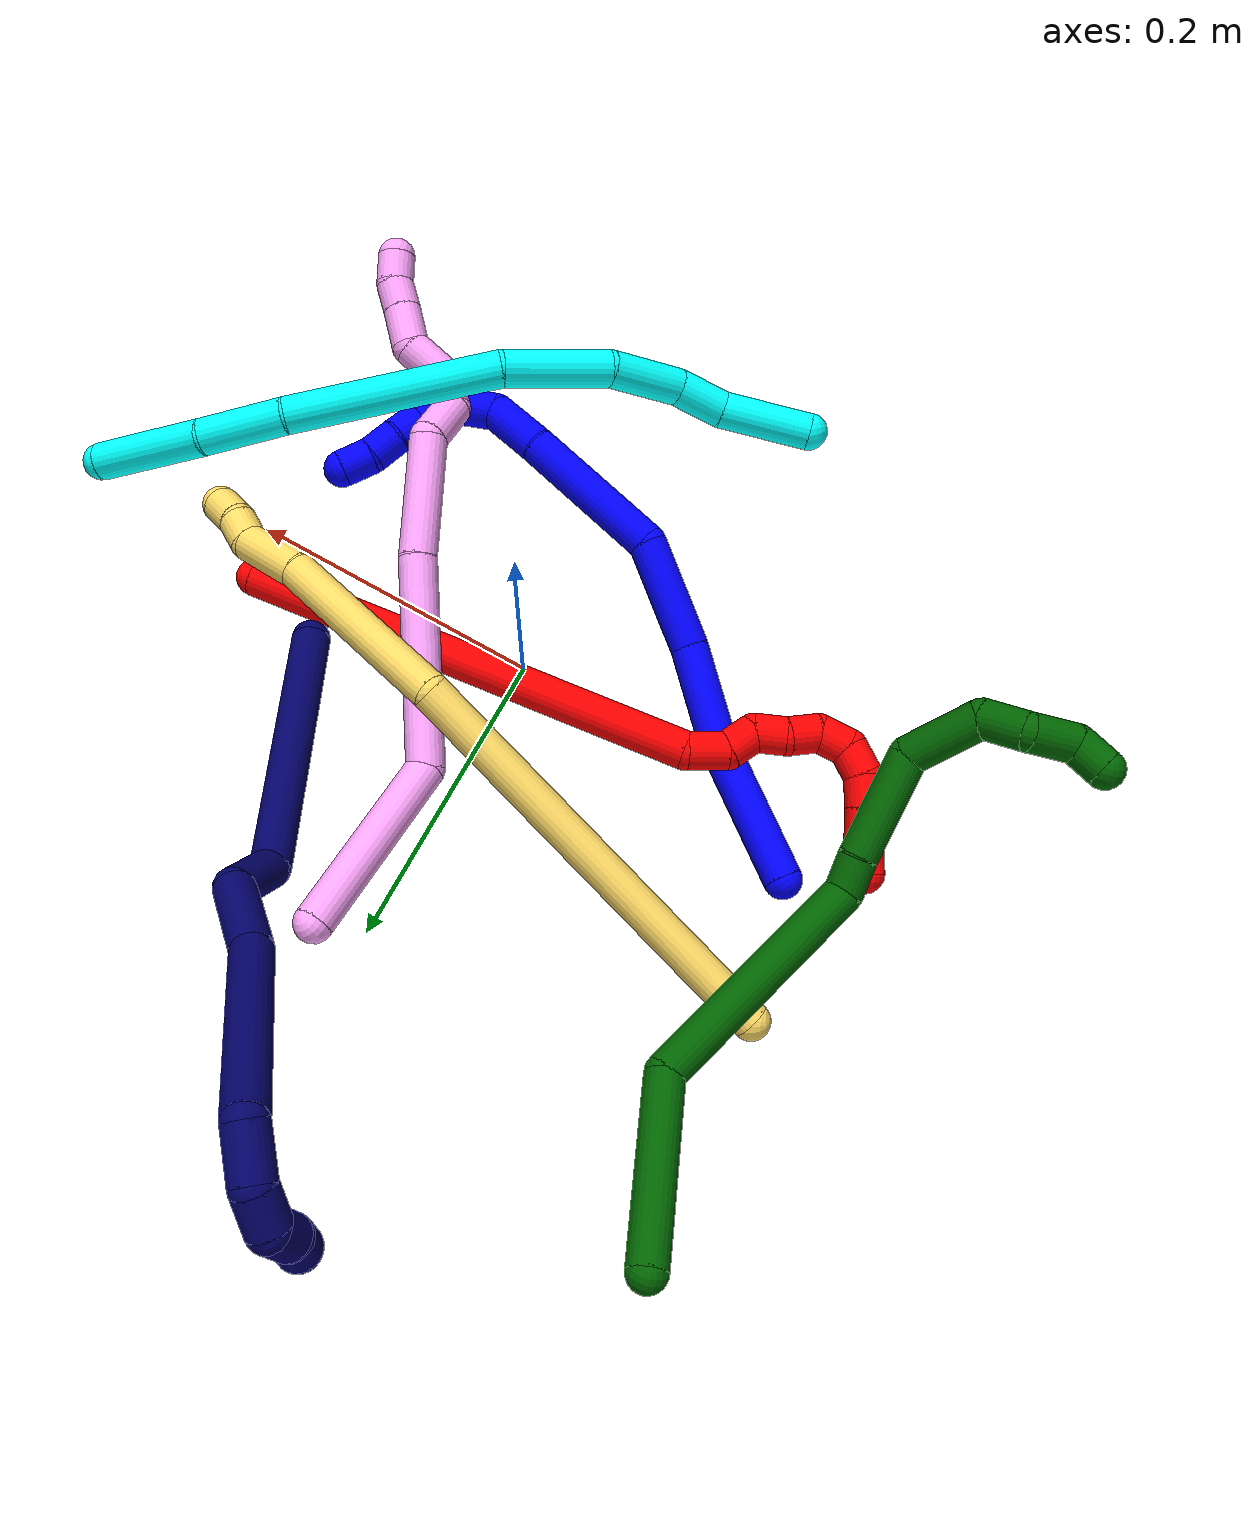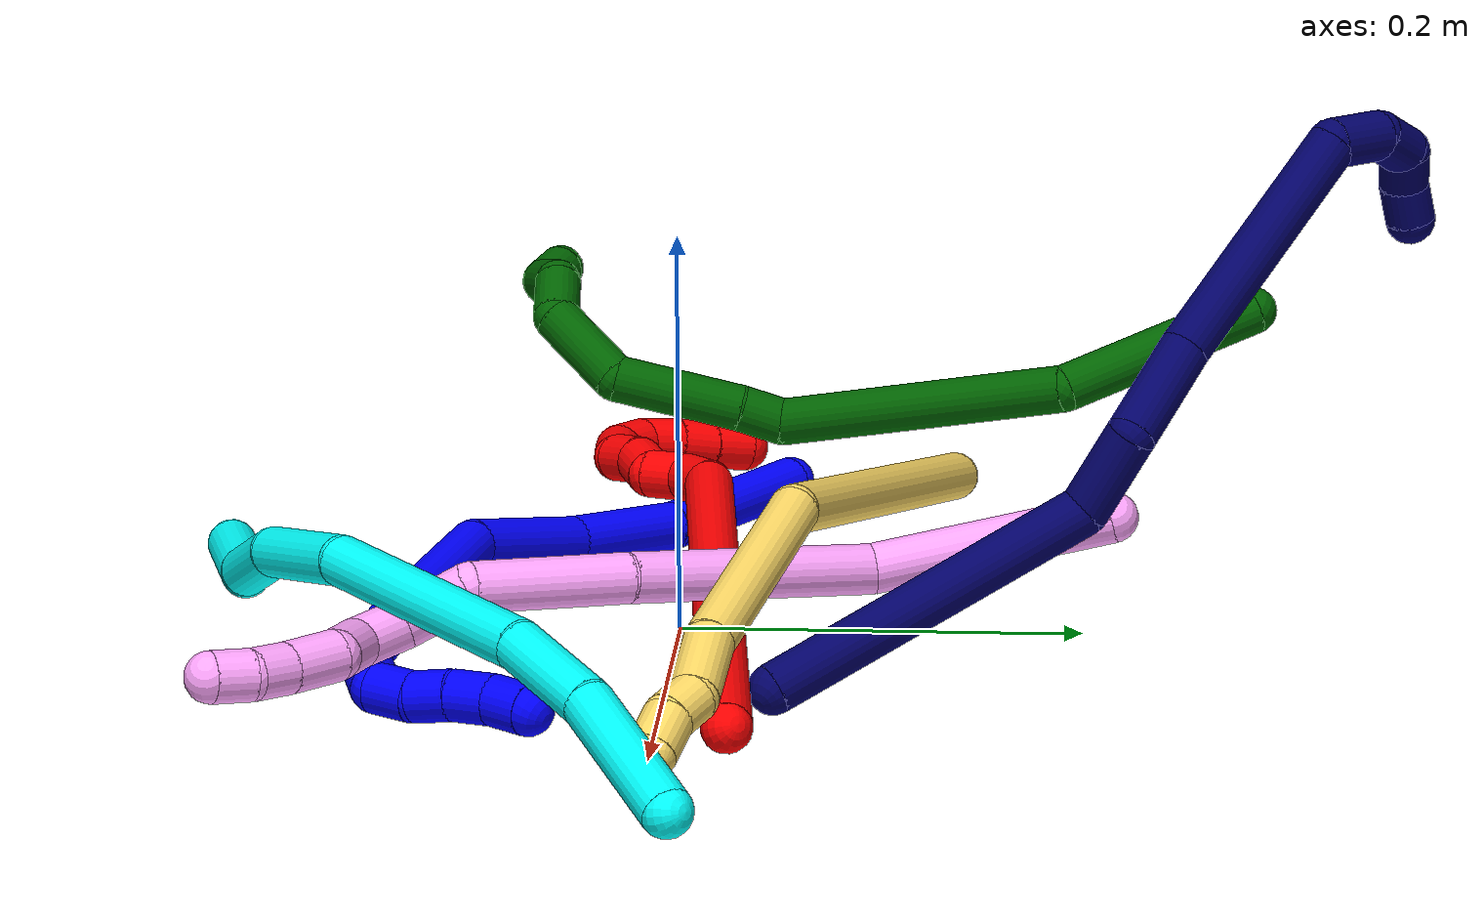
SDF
<sdf version="1.7">
 <world name="default">
  <plugin name="TubeGeneratorPlugin" filename="libtube_generator_plugin.so"/>
  <model name="photoneo_s_sensor">
   <static>1</static>
   <pose>0 0 2 1.57079 1.57079 3.14159</pose>
   <link name="link">
    <inertial><mass>0.1</mass></inertial>
    <sensor name="sensor" type="depth">
     <update_rate>30</update_rate>
     <camera>
      <horizontal_fov>1.22</horizontal_fov>
      <image><width>1920</width><height>1200</height><format>B8G8R8</format></image>
      <clip><near>0.1</near><far>4</far></clip>
      <depth_camera><output>points</output></depth_camera>
     </camera>
     <plugin name="camera_plugin" filename="libgazebo_ros_depth_camera.so">
      <baseline>0.2</baseline>
      <alwaysOn>1</alwaysOn>
      <updateRate>0.0</updateRate>
      <cameraName>camera_ir</cameraName>
      <imageTopicName>/camera/color/image_raw</imageTopicName>
      <cameraInfoTopicName>/camera/color/camera_info</cameraInfoTopicName>
      <depthImageTopicName>/camera/depth/image_raw</depthImageTopicName>
      <depthImageCameraInfoTopicName>/camera/depth/camera_info</depthImageCameraInfoTopicName>
      <pointCloudTopicName>/camera/depth/points</pointCloudTopicName>
      <frameName>fr_optical</frameName>
      <pointCloudCutoff>0.1</pointCloudCutoff>
      <pointCloudCutoffMax>2.0</pointCloudCutoffMax>
      <distortionK1>0</distortionK1>
      <distortionK2>0</distortionK2>
      <distortionK3>0</distortionK3>
      <distortionT1>0</distortionT1>
      <distortionT2>0</distortionT2>
      <CxPrime>0</CxPrime>
      <Cx>0</Cx>
      <Cy>0</Cy>
      <focalLength>0</focalLength>
      <hackBaseline>0</hackBaseline>
     </plugin>
    </sensor>
   </link>
  </model>
  <gravity>0 0 -9.8</gravity>
  <magnetic_field>6e-06 2.3e-05 -4.2e-05</magnetic_field>
  <atmosphere type="adiabatic"/>
  <physics name="default_physics" default="0" type="ode">
   <max_step_size>0.003</max_step_size>
   <real_time_factor>1</real_time_factor>
   <real_time_update_rate>1000</real_time_update_rate>
   <max_contacts>10000</max_contacts>
   <ode>
    <solver>
     <type>quick</type>
     <iters>100</iters>
     <sor>1.3</sor>
     <use_dynamic_moi_rescaling>0</use_dynamic_moi_rescaling>
    </solver>
    <constraints>
     <contact_max_correcting_vel>0</contact_max_correcting_vel>
     <contact_surface_layer>0.001</contact_surface_layer>
     <cfm>0</cfm>
     <erp>0.2</erp>
    </constraints>
   </ode>
  </physics>
  <scene><ambient>0.4 0.4 0.4 1</ambient><background>0.7 0.7 0.7 1</background><shadows>0</shadows></scene>
  <audio><device>default</device></audio>
  <spherical_coordinates>
   <surface_model>EARTH_WGS84</surface_model>
   <latitude_deg>0</latitude_deg>
   <longitude_deg>0</longitude_deg>
   <elevation>0</elevation>
   <heading_deg>0</heading_deg>
  </spherical_coordinates>
  <model name="bin">
   <static>1</static>
   <link name="bottom">
    <collision name="collision-bottom">
     <pose>0 0 -0.01 0 -0 0</pose>
     <geometry><box><size>0.8 0.6 0.02</size></box></geometry>
     <surface>
      <friction><ode><mu>100</mu><mu2>100</mu2></ode></friction>
      <contact><collide_bitmask>65535</collide_bitmask></contact>
     </surface>
    </collision>
   </link>
   <link name="west_wall">
    <collision name="collision-west_wall">
     <pose>-0.41 0 0.1 0 -0 0</pose>
     <geometry><box><size>0.02 0.6 0.2</size></box></geometry>
     <surface>
      <friction><ode><mu>100</mu><mu2>100</mu2></ode></friction>
      <contact><collide_bitmask>65535</collide_bitmask></contact>
     </surface>
    </collision>
   </link>
   <link name="east_wall">
    <collision name="collision-east_wall">
     <pose>0.41 0 0.1 0 -0 0</pose>
     <geometry><box><size>0.02 0.6 0.2</size></box></geometry>
     <surface>
      <friction><ode><mu>100</mu><mu2>100</mu2></ode></friction>
      <contact><collide_bitmask>65535</collide_bitmask></contact>
     </surface>
    </collision>
   </link>
   <link name="south_wall">
    <collision name="collision-south_wall">
     <pose>0 -0.31 0.1 0 -0 0</pose>
     <geometry><box><size>0.8 0.02 0.2</size></box></geometry>
     <surface>
      <friction><ode><mu>100</mu><mu2>100</mu2></ode></friction>
      <contact><collide_bitmask>65535</collide_bitmask></contact>
     </surface>
    </collision>
   </link>
   <link name="north_wall">
    <collision name="collision-north_wall">
     <pose>0 0.31 0.1 0 -0 0</pose>
     <geometry><box><size>0.8 0.02 0.2</size></box></geometry>
     <surface>
      <friction><ode><mu>100</mu><mu2>100</mu2></ode></friction>
      <contact><collide_bitmask>65535</collide_bitmask></contact>
     </surface>
    </collision>
   </link>
  </model>
  <model name="1">
   <static>0</static>
   <link name="1">
    <collision name="collision-cylinder-e_1_1_4">
     <pose>0.040174 -0.025846 0.002964 1.45662 0.996124 0.903143</pose>
     <geometry><cylinder><radius>0.0125</radius><length>0.095723</length></cylinder></geometry>
     <surface>
      <friction><ode><mu>1.16</mu><mu2>1.16</mu2><slip1>0</slip1><slip2>0</slip2></ode></friction>
      <contact><ode><kp>1e+06</kp><kd>1</kd><max_vel>0</max_vel><min_depth>0.001</min_depth></ode></contact>
     </surface>
    </collision>
    <visual name="visual-cylinder-e_1_1_4">
     <pose>0.040174 -0.025846 0.002964 1.45662 0.996124 0.903143</pose>
     <geometry><cylinder><radius>0.0125</radius><length>0.095723</length></cylinder></geometry>
     <material><ambient>0 0 1 1</ambient></material>
    </visual>
    <collision name="collision-cylinder-e_2_4_5">
     <pose>0.109052 -0.067268 0.013447 1.12104 1.0285 0.681549</pose>
     <geometry><cylinder><radius>0.0125</radius><length>0.067026</length></cylinder></geometry>
     <surface>
      <friction><ode><mu>1.16</mu><mu2>1.16</mu2><slip1>0</slip1><slip2>0</slip2></ode></friction>
      <contact><ode><kp>1e+06</kp><kd>1</kd><max_vel>0</max_vel><min_depth>0.001</min_depth></ode></contact>
     </surface>
    </collision>
    <visual name="visual-cylinder-e_2_4_5">
     <pose>0.109052 -0.067268 0.013447 1.12104 1.0285 0.681549</pose>
     <geometry><cylinder><radius>0.0125</radius><length>0.067026</length></cylinder></geometry>
     <material><ambient>0 0 1 1</ambient></material>
    </visual>
    <collision name="collision-cylinder-e_3_5_6">
     <pose>0.171958 -0.095369 0.026352 1.16472 1.19148 0.839758</pose>
     <geometry><cylinder><radius>0.0125</radius><length>0.073636</length></cylinder></geometry>
     <surface>
      <friction><ode><mu>1.16</mu><mu2>1.16</mu2><slip1>0</slip1><slip2>0</slip2></ode></friction>
      <contact><ode><kp>1e+06</kp><kd>1</kd><max_vel>0</max_vel><min_depth>0.001</min_depth></ode></contact>
     </surface>
    </collision>
    <visual name="visual-cylinder-e_3_5_6">
     <pose>0.171958 -0.095369 0.026352 1.16472 1.19148 0.839758</pose>
     <geometry><cylinder><radius>0.0125</radius><length>0.073636</length></cylinder></geometry>
     <material><ambient>0 0 1 1</ambient></material>
    </visual>
    <collision name="collision-cylinder-e_4_6_7">
     <pose>0.24866 -0.1314 0.01611 2.15752 0.984545 1.57136</pose>
     <geometry><cylinder><radius>0.0125</radius><length>0.102041</length></cylinder></geometry>
     <surface>
      <friction><ode><mu>1.16</mu><mu2>1.16</mu2><slip1>0</slip1><slip2>0</slip2></ode></friction>
      <contact><ode><kp>1e+06</kp><kd>1</kd><max_vel>0</max_vel><min_depth>0.001</min_depth></ode></contact>
     </surface>
    </collision>
    <visual name="visual-cylinder-e_4_6_7">
     <pose>0.24866 -0.1314 0.01611 2.15752 0.984545 1.57136</pose>
     <geometry><cylinder><radius>0.0125</radius><length>0.102041</length></cylinder></geometry>
     <material><ambient>0 0 1 1</ambient></material>
    </visual>
    <collision name="collision-cylinder-e_5_7_8">
     <pose>0.306796 -0.166464 -0.006331 2.10346 0.86162 1.35491</pose>
     <geometry><cylinder><radius>0.0125</radius><length>0.041205</length></cylinder></geometry>
     <surface>
      <friction><ode><mu>1.16</mu><mu2>1.16</mu2><slip1>0</slip1><slip2>0</slip2></ode></friction>
      <contact><ode><kp>1e+06</kp><kd>1</kd><max_vel>0</max_vel><min_depth>0.001</min_depth></ode></contact>
     </surface>
    </collision>
    <visual name="visual-cylinder-e_5_7_8">
     <pose>0.306796 -0.166464 -0.006331 2.10346 0.86162 1.35491</pose>
     <geometry><cylinder><radius>0.0125</radius><length>0.041205</length></cylinder></geometry>
     <material><ambient>0 0 1 1</ambient></material>
    </visual>
    <collision name="collision-cylinder-e_6_8_9">
     <pose>0.332969 -0.182255 -0.026379 2.83201 0.648796 2.27268</pose>
     <geometry><cylinder><radius>0.0125</radius><length>0.034879</length></cylinder></geometry>
     <surface>
      <friction><ode><mu>1.16</mu><mu2>1.16</mu2><slip1>0</slip1><slip2>0</slip2></ode></friction>
      <contact><ode><kp>1e+06</kp><kd>1</kd><max_vel>0</max_vel><min_depth>0.001</min_depth></ode></contact>
     </surface>
    </collision>
    <visual name="visual-cylinder-e_6_8_9">
     <pose>0.332969 -0.182255 -0.026379 2.83201 0.648796 2.27268</pose>
     <geometry><cylinder><radius>0.0125</radius><length>0.034879</length></cylinder></geometry>
     <material><ambient>0 0 1 1</ambient></material>
    </visual>
    <collision name="collision-cylinder-e_7_9_10">
     <pose>0.344274 -0.183781 -0.050272 -2.89278 0.06967 -0.543566</pose>
     <geometry><cylinder><radius>0.0125</radius><length>0.022044</length></cylinder></geometry>
     <surface>
      <friction><ode><mu>1.16</mu><mu2>1.16</mu2><slip1>0</slip1><slip2>0</slip2></ode></friction>
      <contact><ode><kp>1e+06</kp><kd>1</kd><max_vel>0</max_vel><min_depth>0.001</min_depth></ode></contact>
     </surface>
    </collision>
    <visual name="visual-cylinder-e_7_9_10">
     <pose>0.344274 -0.183781 -0.050272 -2.89278 0.06967 -0.543566</pose>
     <geometry><cylinder><radius>0.0125</radius><length>0.022044</length></cylinder></geometry>
     <material><ambient>0 0 1 1</ambient></material>
    </visual>
    <collision name="collision-cylinder-e_8_10_11">
     <pose>0.344974 -0.175965 -0.069933 -2.62554 -0.006461 0.02448</pose>
     <geometry><cylinder><radius>0.0125</radius><length>0.020706</length></cylinder></geometry>
     <surface>
      <friction><ode><mu>1.16</mu><mu2>1.16</mu2><slip1>0</slip1><slip2>0</slip2></ode></friction>
      <contact><ode><kp>1e+06</kp><kd>1</kd><max_vel>0</max_vel><min_depth>0.001</min_depth></ode></contact>
     </surface>
    </collision>
    <visual name="visual-cylinder-e_8_10_11">
     <pose>0.344974 -0.175965 -0.069933 -2.62554 -0.006461 0.02448</pose>
     <geometry><cylinder><radius>0.0125</radius><length>0.020706</length></cylinder></geometry>
     <material><ambient>0 0 1 1</ambient></material>
    </visual>
    <collision name="collision-cylinder-e_9_11_12">
     <pose>0.344236 -0.166989 -0.088827 -2.7688 -0.063134 0.331811</pose>
     <geometry><cylinder><radius>0.0125</radius><length>0.02128</length></cylinder></geometry>
     <surface>
      <friction><ode><mu>1.16</mu><mu2>1.16</mu2><slip1>0</slip1><slip2>0</slip2></ode></friction>
      <contact><ode><kp>1e+06</kp><kd>1</kd><max_vel>0</max_vel><min_depth>0.001</min_depth></ode></contact>
     </surface>
    </collision>
    <visual name="visual-cylinder-e_9_11_12">
     <pose>0.344236 -0.166989 -0.088827 -2.7688 -0.063134 0.331811</pose>
     <geometry><cylinder><radius>0.0125</radius><length>0.02128</length></cylinder></geometry>
     <material><ambient>0 0 1 1</ambient></material>
    </visual>
    <collision name="collision-cylinder-e_10_12_2">
     <pose>0.345256 -0.16096 -0.109089 -2.9362 0.158284 -1.31179</pose>
     <geometry><cylinder><radius>0.0125</radius><length>0.021459</length></cylinder></geometry>
     <surface>
      <friction><ode><mu>1.16</mu><mu2>1.16</mu2><slip1>0</slip1><slip2>0</slip2></ode></friction>
      <contact><ode><kp>1e+06</kp><kd>1</kd><max_vel>0</max_vel><min_depth>0.001</min_depth></ode></contact>
     </surface>
    </collision>
    <visual name="visual-cylinder-e_10_12_2">
     <pose>0.345256 -0.16096 -0.109089 -2.9362 0.158284 -1.31179</pose>
     <geometry><cylinder><radius>0.0125</radius><length>0.021459</length></cylinder></geometry>
     <material><ambient>0 0 1 1</ambient></material>
    </visual>
    <collision name="collision-sphere-2">
     <pose>0.346947 -0.158799 -0.119462 0 -0 0</pose>
     <geometry><sphere><radius>0.0125</radius></sphere></geometry>
     <surface>
      <friction><ode><mu>1.16</mu><mu2>1.16</mu2><slip1>0</slip1><slip2>0</slip2></ode></friction>
      <contact><ode><kp>1e+06</kp><kd>1</kd><max_vel>0</max_vel><min_depth>0.001</min_depth></ode></contact>
     </surface>
    </collision>
    <visual name="visual-sphere-2">
     <pose>0.346947 -0.158799 -0.119462 0 -0 0</pose>
     <geometry><sphere><radius>0.0125</radius></sphere></geometry>
     <material><ambient>0 0 1 1</ambient></material>
    </visual>
    <collision name="collision-sphere-12">
     <pose>0.343565 -0.163121 -0.098717 0 -0 0</pose>
     <geometry><sphere><radius>0.0125</radius></sphere></geometry>
     <surface>
      <friction><ode><mu>1.16</mu><mu2>1.16</mu2><slip1>0</slip1><slip2>0</slip2></ode></friction>
      <contact><ode><kp>1e+06</kp><kd>1</kd><max_vel>0</max_vel><min_depth>0.001</min_depth></ode></contact>
     </surface>
    </collision>
    <visual name="visual-sphere-12">
     <pose>0.343565 -0.163121 -0.098717 0 -0 0</pose>
     <geometry><sphere><radius>0.0125</radius></sphere></geometry>
     <material><ambient>0 0 1 1</ambient></material>
    </visual>
    <collision name="collision-sphere-11">
     <pose>0.344907 -0.170856 -0.078937 0 -0 0</pose>
     <geometry><sphere><radius>0.0125</radius></sphere></geometry>
     <surface>
      <friction><ode><mu>1.16</mu><mu2>1.16</mu2><slip1>0</slip1><slip2>0</slip2></ode></friction>
      <contact><ode><kp>1e+06</kp><kd>1</kd><max_vel>0</max_vel><min_depth>0.001</min_depth></ode></contact>
     </surface>
    </collision>
    <visual name="visual-sphere-11">
     <pose>0.344907 -0.170856 -0.078937 0 -0 0</pose>
     <geometry><sphere><radius>0.0125</radius></sphere></geometry>
     <material><ambient>0 0 1 1</ambient></material>
    </visual>
    <collision name="collision-sphere-10">
     <pose>0.345041 -0.181073 -0.060928 0 -0 0</pose>
     <geometry><sphere><radius>0.0125</radius></sphere></geometry>
     <surface>
      <friction><ode><mu>1.16</mu><mu2>1.16</mu2><slip1>0</slip1><slip2>0</slip2></ode></friction>
      <contact><ode><kp>1e+06</kp><kd>1</kd><max_vel>0</max_vel><min_depth>0.001</min_depth></ode></contact>
     </surface>
    </collision>
    <visual name="visual-sphere-10">
     <pose>0.345041 -0.181073 -0.060928 0 -0 0</pose>
     <geometry><sphere><radius>0.0125</radius></sphere></geometry>
     <material><ambient>0 0 1 1</ambient></material>
    </visual>
    <collision name="collision-sphere-9">
     <pose>0.343506 -0.186489 -0.039615 0 -0 0</pose>
     <geometry><sphere><radius>0.0125</radius></sphere></geometry>
     <surface>
      <friction><ode><mu>1.16</mu><mu2>1.16</mu2><slip1>0</slip1><slip2>0</slip2></ode></friction>
      <contact><ode><kp>1e+06</kp><kd>1</kd><max_vel>0</max_vel><min_depth>0.001</min_depth></ode></contact>
     </surface>
    </collision>
    <visual name="visual-sphere-9">
     <pose>0.343506 -0.186489 -0.039615 0 -0 0</pose>
     <geometry><sphere><radius>0.0125</radius></sphere></geometry>
     <material><ambient>0 0 1 1</ambient></material>
    </visual>
    <collision name="collision-sphere-4">
     <pose>0.080347 -0.051692 0.005928 0 -0 0</pose>
     <geometry><sphere><radius>0.0125</radius></sphere></geometry>
     <surface>
      <friction><ode><mu>1.16</mu><mu2>1.16</mu2><slip1>0</slip1><slip2>0</slip2></ode></friction>
      <contact><ode><kp>1e+06</kp><kd>1</kd><max_vel>0</max_vel><min_depth>0.001</min_depth></ode></contact>
     </surface>
    </collision>
    <visual name="visual-sphere-4">
     <pose>0.080347 -0.051692 0.005928 0 -0 0</pose>
     <geometry><sphere><radius>0.0125</radius></sphere></geometry>
     <material><ambient>0 0 1 1</ambient></material>
    </visual>
    <collision name="collision-sphere-1">
     <geometry><sphere><radius>0.0125</radius></sphere></geometry>
     <surface>
      <friction><ode><mu>1.16</mu><mu2>1.16</mu2><slip1>0</slip1><slip2>0</slip2></ode></friction>
      <contact><ode><kp>1e+06</kp><kd>1</kd><max_vel>0</max_vel><min_depth>0.001</min_depth></ode></contact>
     </surface>
    </collision>
    <visual name="visual-sphere-1">
     <geometry><sphere><radius>0.0125</radius></sphere></geometry>
     <material><ambient>0 0 1 1</ambient></material>
    </visual>
    <collision name="collision-sphere-8">
     <pose>0.322432 -0.178021 -0.013144 0 -0 0</pose>
     <geometry><sphere><radius>0.0125</radius></sphere></geometry>
     <surface>
      <friction><ode><mu>1.16</mu><mu2>1.16</mu2><slip1>0</slip1><slip2>0</slip2></ode></friction>
      <contact><ode><kp>1e+06</kp><kd>1</kd><max_vel>0</max_vel><min_depth>0.001</min_depth></ode></contact>
     </surface>
    </collision>
    <visual name="visual-sphere-8">
     <pose>0.322432 -0.178021 -0.013144 0 -0 0</pose>
     <geometry><sphere><radius>0.0125</radius></sphere></geometry>
     <material><ambient>0 0 1 1</ambient></material>
    </visual>
    <collision name="collision-sphere-5">
     <pose>0.137757 -0.082845 0.020967 0 -0 0</pose>
     <geometry><sphere><radius>0.0125</radius></sphere></geometry>
     <surface>
      <friction><ode><mu>1.16</mu><mu2>1.16</mu2><slip1>0</slip1><slip2>0</slip2></ode></friction>
      <contact><ode><kp>1e+06</kp><kd>1</kd><max_vel>0</max_vel><min_depth>0.001</min_depth></ode></contact>
     </surface>
    </collision>
    <visual name="visual-sphere-5">
     <pose>0.137757 -0.082845 0.020967 0 -0 0</pose>
     <geometry><sphere><radius>0.0125</radius></sphere></geometry>
     <material><ambient>0 0 1 1</ambient></material>
    </visual>
    <collision name="collision-sphere-6">
     <pose>0.206159 -0.107894 0.031737 0 -0 0</pose>
     <geometry><sphere><radius>0.0125</radius></sphere></geometry>
     <surface>
      <friction><ode><mu>1.16</mu><mu2>1.16</mu2><slip1>0</slip1><slip2>0</slip2></ode></friction>
      <contact><ode><kp>1e+06</kp><kd>1</kd><max_vel>0</max_vel><min_depth>0.001</min_depth></ode></contact>
     </surface>
    </collision>
    <visual name="visual-sphere-6">
     <pose>0.206159 -0.107894 0.031737 0 -0 0</pose>
     <geometry><sphere><radius>0.0125</radius></sphere></geometry>
     <material><ambient>0 0 1 1</ambient></material>
    </visual>
    <collision name="collision-sphere-7">
     <pose>0.291161 -0.154906 0.000483 0 -0 0</pose>
     <geometry><sphere><radius>0.0125</radius></sphere></geometry>
     <surface>
      <friction><ode><mu>1.16</mu><mu2>1.16</mu2><slip1>0</slip1><slip2>0</slip2></ode></friction>
      <contact><ode><kp>1e+06</kp><kd>1</kd><max_vel>0</max_vel><min_depth>0.001</min_depth></ode></contact>
     </surface>
    </collision>
    <visual name="visual-sphere-7">
     <pose>0.291161 -0.154906 0.000483 0 -0 0</pose>
     <geometry><sphere><radius>0.0125</radius></sphere></geometry>
     <material><ambient>0 0 1 1</ambient></material>
    </visual>
    <inertial>
     <pose>0.205825 -0.110664 -0.006398 0 -0 0</pose>
     <mass>0.5</mass>
     <inertia>
      <ixx>0.000185</ixx>
      <ixy>0</ixy>
      <ixz>0</ixz>
      <iyy>0.000275</iyy>
      <iyz>0</iyz>
      <izz>-0.000105</izz>
     </inertia>
    </inertial>
   </link>
   <pose>-0.212737 0.043578 0.014528 1.24814 -0.497996 -0.415307</pose>
  </model>
  <model name="2">
   <static>0</static>
   <link name="2">
    <collision name="collision-cylinder-e_1_1_4">
     <pose>-0.095933 -0.015489 -0.119954 3.01317 -0.67056 -2.77664</pose>
     <geometry><cylinder><radius>0.0125</radius><length>0.308753</length></cylinder></geometry>
     <surface>
      <friction><ode><mu>1.16</mu><mu2>1.16</mu2><slip1>0</slip1><slip2>0</slip2></ode></friction>
      <contact><ode><kp>1e+06</kp><kd>1</kd><max_vel>0</max_vel><min_depth>0.001</min_depth></ode></contact>
     </surface>
    </collision>
    <visual name="visual-cylinder-e_1_1_4">
     <pose>-0.095933 -0.015489 -0.119954 3.01317 -0.67056 -2.77664</pose>
     <geometry><cylinder><radius>0.0125</radius><length>0.308753</length></cylinder></geometry>
     <material><ambient>1 0 0 1</ambient></material>
    </visual>
    <collision name="collision-cylinder-e_2_4_5">
     <pose>-0.194218 -0.03368 -0.252413 2.92888 -0.18172 -1.41296</pose>
     <geometry><cylinder><radius>0.0125</radius><length>0.026015</length></cylinder></geometry>
     <surface>
      <friction><ode><mu>1.16</mu><mu2>1.16</mu2><slip1>0</slip1><slip2>0</slip2></ode></friction>
      <contact><ode><kp>1e+06</kp><kd>1</kd><max_vel>0</max_vel><min_depth>0.001</min_depth></ode></contact>
     </surface>
    </collision>
    <visual name="visual-cylinder-e_2_4_5">
     <pose>-0.194218 -0.03368 -0.252413 2.92888 -0.18172 -1.41296</pose>
     <geometry><cylinder><radius>0.0125</radius><length>0.026015</length></cylinder></geometry>
     <material><ambient>1 0 0 1</ambient></material>
    </visual>
    <collision name="collision-cylinder-e_3_5_6">
     <pose>-0.193649 -0.041867 -0.273531 2.57442 0.278439 0.896339</pose>
     <geometry><cylinder><radius>0.0125</radius><length>0.021243</length></cylinder></geometry>
     <surface>
      <friction><ode><mu>1.16</mu><mu2>1.16</mu2><slip1>0</slip1><slip2>0</slip2></ode></friction>
      <contact><ode><kp>1e+06</kp><kd>1</kd><max_vel>0</max_vel><min_depth>0.001</min_depth></ode></contact>
     </surface>
    </collision>
    <visual name="visual-cylinder-e_3_5_6">
     <pose>-0.193649 -0.041867 -0.273531 2.57442 0.278439 0.896339</pose>
     <geometry><cylinder><radius>0.0125</radius><length>0.021243</length></cylinder></geometry>
     <material><ambient>1 0 0 1</ambient></material>
    </visual>
    <collision name="collision-cylinder-e_4_6_7">
     <pose>-0.195075 -0.05012 -0.291314 2.84856 -0.425899 -1.94383</pose>
     <geometry><cylinder><radius>0.0125</radius><length>0.021035</length></cylinder></geometry>
     <surface>
      <friction><ode><mu>1.16</mu><mu2>1.16</mu2><slip1>0</slip1><slip2>0</slip2></ode></friction>
      <contact><ode><kp>1e+06</kp><kd>1</kd><max_vel>0</max_vel><min_depth>0.001</min_depth></ode></contact>
     </surface>
    </collision>
    <visual name="visual-cylinder-e_4_6_7">
     <pose>-0.195075 -0.05012 -0.291314 2.84856 -0.425899 -1.94383</pose>
     <geometry><cylinder><radius>0.0125</radius><length>0.021035</length></cylinder></geometry>
     <material><ambient>1 0 0 1</ambient></material>
    </visual>
    <collision name="collision-cylinder-e_5_7_8">
     <pose>-0.199966 -0.055363 -0.310571 2.90095 -0.052542 -0.428009</pose>
     <geometry><cylinder><radius>0.0125</radius><length>0.020802</length></cylinder></geometry>
     <surface>
      <friction><ode><mu>1.16</mu><mu2>1.16</mu2><slip1>0</slip1><slip2>0</slip2></ode></friction>
      <contact><ode><kp>1e+06</kp><kd>1</kd><max_vel>0</max_vel><min_depth>0.001</min_depth></ode></contact>
     </surface>
    </collision>
    <visual name="visual-cylinder-e_5_7_8">
     <pose>-0.199966 -0.055363 -0.310571 2.90095 -0.052542 -0.428009</pose>
     <geometry><cylinder><radius>0.0125</radius><length>0.020802</length></cylinder></geometry>
     <material><ambient>1 0 0 1</ambient></material>
    </visual>
    <collision name="collision-cylinder-e_6_8_9">
     <pose>-0.20662 -0.05753 -0.328873 -3.10414 -0.639014 3.02849</pose>
     <geometry><cylinder><radius>0.0125</radius><length>0.020482</length></cylinder></geometry>
     <surface>
      <friction><ode><mu>1.16</mu><mu2>1.16</mu2><slip1>0</slip1><slip2>0</slip2></ode></friction>
      <contact><ode><kp>1e+06</kp><kd>1</kd><max_vel>0</max_vel><min_depth>0.001</min_depth></ode></contact>
     </surface>
    </collision>
    <visual name="visual-cylinder-e_6_8_9">
     <pose>-0.20662 -0.05753 -0.328873 -3.10414 -0.639014 3.02849</pose>
     <geometry><cylinder><radius>0.0125</radius><length>0.020482</length></cylinder></geometry>
     <material><ambient>1 0 0 1</ambient></material>
    </visual>
    <collision name="collision-cylinder-e_7_9_10">
     <pose>-0.221071 -0.053058 -0.340777 -2.29588 -0.982618 1.74308</pose>
     <geometry><cylinder><radius>0.0125</radius><length>0.020056</length></cylinder></geometry>
     <surface>
      <friction><ode><mu>1.16</mu><mu2>1.16</mu2><slip1>0</slip1><slip2>0</slip2></ode></friction>
      <contact><ode><kp>1e+06</kp><kd>1</kd><max_vel>0</max_vel><min_depth>0.001</min_depth></ode></contact>
     </surface>
    </collision>
    <visual name="visual-cylinder-e_7_9_10">
     <pose>-0.221071 -0.053058 -0.340777 -2.29588 -0.982618 1.74308</pose>
     <geometry><cylinder><radius>0.0125</radius><length>0.020056</length></cylinder></geometry>
     <material><ambient>1 0 0 1</ambient></material>
    </visual>
    <collision name="collision-cylinder-e_8_10_11">
     <pose>-0.237079 -0.042258 -0.344626 -1.59471 -0.857095 0.875313</pose>
     <geometry><cylinder><radius>0.0125</radius><length>0.020279</length></cylinder></geometry>
     <surface>
      <friction><ode><mu>1.16</mu><mu2>1.16</mu2><slip1>0</slip1><slip2>0</slip2></ode></friction>
      <contact><ode><kp>1e+06</kp><kd>1</kd><max_vel>0</max_vel><min_depth>0.001</min_depth></ode></contact>
     </surface>
    </collision>
    <visual name="visual-cylinder-e_8_10_11">
     <pose>-0.237079 -0.042258 -0.344626 -1.59471 -0.857095 0.875313</pose>
     <geometry><cylinder><radius>0.0125</radius><length>0.020279</length></cylinder></geometry>
     <material><ambient>1 0 0 1</ambient></material>
    </visual>
    <collision name="collision-cylinder-e_9_11_12">
     <pose>-0.251746 -0.028217 -0.344679 -1.55653 -0.757439 0.747687</pose>
     <geometry><cylinder><radius>0.0125</radius><length>0.020383</length></cylinder></geometry>
     <surface>
      <friction><ode><mu>1.16</mu><mu2>1.16</mu2><slip1>0</slip1><slip2>0</slip2></ode></friction>
      <contact><ode><kp>1e+06</kp><kd>1</kd><max_vel>0</max_vel><min_depth>0.001</min_depth></ode></contact>
     </surface>
    </collision>
    <visual name="visual-cylinder-e_9_11_12">
     <pose>-0.251746 -0.028217 -0.344679 -1.55653 -0.757439 0.747687</pose>
     <geometry><cylinder><radius>0.0125</radius><length>0.020383</length></cylinder></geometry>
     <material><ambient>1 0 0 1</ambient></material>
    </visual>
    <collision name="collision-cylinder-e_10_12_2">
     <pose>-0.266315 -0.01357 -0.344708 -1.5894 -0.807161 0.820688</pose>
     <geometry><cylinder><radius>0.0125</radius><length>0.020952</length></cylinder></geometry>
     <surface>
      <friction><ode><mu>1.16</mu><mu2>1.16</mu2><slip1>0</slip1><slip2>0</slip2></ode></friction>
      <contact><ode><kp>1e+06</kp><kd>1</kd><max_vel>0</max_vel><min_depth>0.001</min_depth></ode></contact>
     </surface>
    </collision>
    <visual name="visual-cylinder-e_10_12_2">
     <pose>-0.266315 -0.01357 -0.344708 -1.5894 -0.807161 0.820688</pose>
     <geometry><cylinder><radius>0.0125</radius><length>0.020952</length></cylinder></geometry>
     <material><ambient>1 0 0 1</ambient></material>
    </visual>
    <collision name="collision-sphere-2">
     <pose>-0.273882 -0.006326 -0.344843 0 -0 0</pose>
     <geometry><sphere><radius>0.0125</radius></sphere></geometry>
     <surface>
      <friction><ode><mu>1.16</mu><mu2>1.16</mu2><slip1>0</slip1><slip2>0</slip2></ode></friction>
      <contact><ode><kp>1e+06</kp><kd>1</kd><max_vel>0</max_vel><min_depth>0.001</min_depth></ode></contact>
     </surface>
    </collision>
    <visual name="visual-sphere-2">
     <pose>-0.273882 -0.006326 -0.344843 0 -0 0</pose>
     <geometry><sphere><radius>0.0125</radius></sphere></geometry>
     <material><ambient>1 0 0 1</ambient></material>
    </visual>
    <collision name="collision-sphere-12">
     <pose>-0.258748 -0.020813 -0.344573 0 -0 0</pose>
     <geometry><sphere><radius>0.0125</radius></sphere></geometry>
     <surface>
      <friction><ode><mu>1.16</mu><mu2>1.16</mu2><slip1>0</slip1><slip2>0</slip2></ode></friction>
      <contact><ode><kp>1e+06</kp><kd>1</kd><max_vel>0</max_vel><min_depth>0.001</min_depth></ode></contact>
     </surface>
    </collision>
    <visual name="visual-sphere-12">
     <pose>-0.258748 -0.020813 -0.344573 0 -0 0</pose>
     <geometry><sphere><radius>0.0125</radius></sphere></geometry>
     <material><ambient>1 0 0 1</ambient></material>
    </visual>
    <collision name="collision-sphere-11">
     <pose>-0.244744 -0.035622 -0.344785 0 -0 0</pose>
     <geometry><sphere><radius>0.0125</radius></sphere></geometry>
     <surface>
      <friction><ode><mu>1.16</mu><mu2>1.16</mu2><slip1>0</slip1><slip2>0</slip2></ode></friction>
      <contact><ode><kp>1e+06</kp><kd>1</kd><max_vel>0</max_vel><min_depth>0.001</min_depth></ode></contact>
     </surface>
    </collision>
    <visual name="visual-sphere-11">
     <pose>-0.244744 -0.035622 -0.344785 0 -0 0</pose>
     <geometry><sphere><radius>0.0125</radius></sphere></geometry>
     <material><ambient>1 0 0 1</ambient></material>
    </visual>
    <collision name="collision-sphere-10">
     <pose>-0.229414 -0.048894 -0.344467 0 -0 0</pose>
     <geometry><sphere><radius>0.0125</radius></sphere></geometry>
     <surface>
      <friction><ode><mu>1.16</mu><mu2>1.16</mu2><slip1>0</slip1><slip2>0</slip2></ode></friction>
      <contact><ode><kp>1e+06</kp><kd>1</kd><max_vel>0</max_vel><min_depth>0.001</min_depth></ode></contact>
     </surface>
    </collision>
    <visual name="visual-sphere-10">
     <pose>-0.229414 -0.048894 -0.344467 0 -0 0</pose>
     <geometry><sphere><radius>0.0125</radius></sphere></geometry>
     <material><ambient>1 0 0 1</ambient></material>
    </visual>
    <collision name="collision-sphere-9">
     <pose>-0.212728 -0.057222 -0.337087 0 -0 0</pose>
     <geometry><sphere><radius>0.0125</radius></sphere></geometry>
     <surface>
      <friction><ode><mu>1.16</mu><mu2>1.16</mu2><slip1>0</slip1><slip2>0</slip2></ode></friction>
      <contact><ode><kp>1e+06</kp><kd>1</kd><max_vel>0</max_vel><min_depth>0.001</min_depth></ode></contact>
     </surface>
    </collision>
    <visual name="visual-sphere-9">
     <pose>-0.212728 -0.057222 -0.337087 0 -0 0</pose>
     <geometry><sphere><radius>0.0125</radius></sphere></geometry>
     <material><ambient>1 0 0 1</ambient></material>
    </visual>
    <collision name="collision-sphere-4">
     <pose>-0.191867 -0.030979 -0.239908 0 -0 0</pose>
     <geometry><sphere><radius>0.0125</radius></sphere></geometry>
     <surface>
      <friction><ode><mu>1.16</mu><mu2>1.16</mu2><slip1>0</slip1><slip2>0</slip2></ode></friction>
      <contact><ode><kp>1e+06</kp><kd>1</kd><max_vel>0</max_vel><min_depth>0.001</min_depth></ode></contact>
     </surface>
    </collision>
    <visual name="visual-sphere-4">
     <pose>-0.191867 -0.030979 -0.239908 0 -0 0</pose>
     <geometry><sphere><radius>0.0125</radius></sphere></geometry>
     <material><ambient>1 0 0 1</ambient></material>
    </visual>
    <collision name="collision-sphere-1">
     <geometry><sphere><radius>0.0125</radius></sphere></geometry>
     <surface>
      <friction><ode><mu>1.16</mu><mu2>1.16</mu2><slip1>0</slip1><slip2>0</slip2></ode></friction>
      <contact><ode><kp>1e+06</kp><kd>1</kd><max_vel>0</max_vel><min_depth>0.001</min_depth></ode></contact>
     </surface>
    </collision>
    <visual name="visual-sphere-1">
     <geometry><sphere><radius>0.0125</radius></sphere></geometry>
     <material><ambient>1 0 0 1</ambient></material>
    </visual>
    <collision name="collision-sphere-8">
     <pose>-0.200512 -0.057838 -0.320658 0 -0 0</pose>
     <geometry><sphere><radius>0.0125</radius></sphere></geometry>
     <surface>
      <friction><ode><mu>1.16</mu><mu2>1.16</mu2><slip1>0</slip1><slip2>0</slip2></ode></friction>
      <contact><ode><kp>1e+06</kp><kd>1</kd><max_vel>0</max_vel><min_depth>0.001</min_depth></ode></contact>
     </surface>
    </collision>
    <visual name="visual-sphere-8">
     <pose>-0.200512 -0.057838 -0.320658 0 -0 0</pose>
     <geometry><sphere><radius>0.0125</radius></sphere></geometry>
     <material><ambient>1 0 0 1</ambient></material>
    </visual>
    <collision name="collision-sphere-5">
     <pose>-0.196568 -0.03638 -0.264918 0 -0 0</pose>
     <geometry><sphere><radius>0.0125</radius></sphere></geometry>
     <surface>
      <friction><ode><mu>1.16</mu><mu2>1.16</mu2><slip1>0</slip1><slip2>0</slip2></ode></friction>
      <contact><ode><kp>1e+06</kp><kd>1</kd><max_vel>0</max_vel><min_depth>0.001</min_depth></ode></contact>
     </surface>
    </collision>
    <visual name="visual-sphere-5">
     <pose>-0.196568 -0.03638 -0.264918 0 -0 0</pose>
     <geometry><sphere><radius>0.0125</radius></sphere></geometry>
     <material><ambient>1 0 0 1</ambient></material>
    </visual>
    <collision name="collision-sphere-6">
     <pose>-0.19073 -0.047354 -0.282145 0 -0 0</pose>
     <geometry><sphere><radius>0.0125</radius></sphere></geometry>
     <surface>
      <friction><ode><mu>1.16</mu><mu2>1.16</mu2><slip1>0</slip1><slip2>0</slip2></ode></friction>
      <contact><ode><kp>1e+06</kp><kd>1</kd><max_vel>0</max_vel><min_depth>0.001</min_depth></ode></contact>
     </surface>
    </collision>
    <visual name="visual-sphere-6">
     <pose>-0.19073 -0.047354 -0.282145 0 -0 0</pose>
     <geometry><sphere><radius>0.0125</radius></sphere></geometry>
     <material><ambient>1 0 0 1</ambient></material>
    </visual>
    <collision name="collision-sphere-7">
     <pose>-0.19942 -0.052887 -0.300484 0 -0 0</pose>
     <geometry><sphere><radius>0.0125</radius></sphere></geometry>
     <surface>
      <friction><ode><mu>1.16</mu><mu2>1.16</mu2><slip1>0</slip1><slip2>0</slip2></ode></friction>
      <contact><ode><kp>1e+06</kp><kd>1</kd><max_vel>0</max_vel><min_depth>0.001</min_depth></ode></contact>
     </surface>
    </collision>
    <visual name="visual-sphere-7">
     <pose>-0.19942 -0.052887 -0.300484 0 -0 0</pose>
     <geometry><sphere><radius>0.0125</radius></sphere></geometry>
     <material><ambient>1 0 0 1</ambient></material>
    </visual>
    <inertial>
     <pose>-0.142468 -0.025426 -0.193618 0 -0 0</pose>
     <mass>0.5</mass>
     <inertia>
      <ixx>-0.002511</ixx>
      <ixy>0</ixy>
      <ixz>0</ixz>
      <iyy>0.001667</iyy>
      <iyz>0</iyz>
      <izz>0.001757</izz>
     </inertia>
    </inertial>
   </link>
   <pose>0.1845 0.035342 0.01149 -1.10958 0.523492 -0.743257</pose>
  </model>
  <model name="3">
   <static>0</static>
   <link name="3">
    <collision name="collision-cylinder-e_1_1_4">
     <pose>-0.020624 -0.011979 -0.031499 2.7782 -0.549178 -1.98577</pose>
     <geometry><cylinder><radius>0.0125</radius><length>0.07902</length></cylinder></geometry>
     <surface>
      <friction><ode><mu>1.16</mu><mu2>1.16</mu2><slip1>0</slip1><slip2>0</slip2></ode></friction>
      <contact><ode><kp>1e+06</kp><kd>1</kd><max_vel>0</max_vel><min_depth>0.001</min_depth></ode></contact>
     </surface>
    </collision>
    <visual name="visual-cylinder-e_1_1_4">
     <pose>-0.020624 -0.011979 -0.031499 2.7782 -0.549178 -1.98577</pose>
     <geometry><cylinder><radius>0.0125</radius><length>0.07902</length></cylinder></geometry>
     <material><ambient>0.003922 1 0.996078 1</ambient></material>
    </visual>
    <collision name="collision-cylinder-e_2_4_5">
     <pose>-0.05222 -0.030971 -0.088892 2.87706 -0.38826 -1.95175</pose>
     <geometry><cylinder><radius>0.0125</radius><length>0.057968</length></cylinder></geometry>
     <surface>
      <friction><ode><mu>1.16</mu><mu2>1.16</mu2><slip1>0</slip1><slip2>0</slip2></ode></friction>
      <contact><ode><kp>1e+06</kp><kd>1</kd><max_vel>0</max_vel><min_depth>0.001</min_depth></ode></contact>
     </surface>
    </collision>
    <visual name="visual-cylinder-e_2_4_5">
     <pose>-0.05222 -0.030971 -0.088892 2.87706 -0.38826 -1.95175</pose>
     <geometry><cylinder><radius>0.0125</radius><length>0.057968</length></cylinder></geometry>
     <material><ambient>0.003922 1 0.996078 1</ambient></material>
    </visual>
    <collision name="collision-cylinder-e_3_5_6">
     <pose>-0.081136 -0.047214 -0.183939 3.00893 -0.251729 -2.17469</pose>
     <geometry><cylinder><radius>0.0125</radius><length>0.144074</length></cylinder></geometry>
     <surface>
      <friction><ode><mu>1.16</mu><mu2>1.16</mu2><slip1>0</slip1><slip2>0</slip2></ode></friction>
      <contact><ode><kp>1e+06</kp><kd>1</kd><max_vel>0</max_vel><min_depth>0.001</min_depth></ode></contact>
     </surface>
    </collision>
    <visual name="visual-cylinder-e_3_5_6">
     <pose>-0.081136 -0.047214 -0.183939 3.00893 -0.251729 -2.17469</pose>
     <geometry><cylinder><radius>0.0125</radius><length>0.144074</length></cylinder></geometry>
     <material><ambient>0.003922 1 0.996078 1</ambient></material>
    </visual>
    <collision name="collision-cylinder-e_4_6_7">
     <pose>-0.106544 -0.051724 -0.288269 -3.00823 -0.207327 2.00032</pose>
     <geometry><cylinder><radius>0.0125</radius><length>0.072537</length></cylinder></geometry>
     <surface>
      <friction><ode><mu>1.16</mu><mu2>1.16</mu2><slip1>0</slip1><slip2>0</slip2></ode></friction>
      <contact><ode><kp>1e+06</kp><kd>1</kd><max_vel>0</max_vel><min_depth>0.001</min_depth></ode></contact>
     </surface>
    </collision>
    <visual name="visual-cylinder-e_4_6_7">
     <pose>-0.106544 -0.051724 -0.288269 -3.00823 -0.207327 2.00032</pose>
     <geometry><cylinder><radius>0.0125</radius><length>0.072537</length></cylinder></geometry>
     <material><ambient>0.003922 1 0.996078 1</ambient></material>
    </visual>
    <collision name="collision-cylinder-e_5_7_8">
     <pose>-0.117548 -0.036427 -0.346566 -2.7125 -0.138276 0.615413</pose>
     <geometry><cylinder><radius>0.0125</radius><length>0.051339</length></cylinder></geometry>
     <surface>
      <friction><ode><mu>1.16</mu><mu2>1.16</mu2><slip1>0</slip1><slip2>0</slip2></ode></friction>
      <contact><ode><kp>1e+06</kp><kd>1</kd><max_vel>0</max_vel><min_depth>0.001</min_depth></ode></contact>
     </surface>
    </collision>
    <visual name="visual-cylinder-e_5_7_8">
     <pose>-0.117548 -0.036427 -0.346566 -2.7125 -0.138276 0.615413</pose>
     <geometry><cylinder><radius>0.0125</radius><length>0.051339</length></cylinder></geometry>
     <material><ambient>0.003922 1 0.996078 1</ambient></material>
    </visual>
    <collision name="collision-cylinder-e_6_8_9">
     <pose>-0.128296 -0.017608 -0.382821 -2.58128 -0.435204 1.31041</pose>
     <geometry><cylinder><radius>0.0125</radius><length>0.034202</length></cylinder></geometry>
     <surface>
      <friction><ode><mu>1.16</mu><mu2>1.16</mu2><slip1>0</slip1><slip2>0</slip2></ode></friction>
      <contact><ode><kp>1e+06</kp><kd>1</kd><max_vel>0</max_vel><min_depth>0.001</min_depth></ode></contact>
     </surface>
    </collision>
    <visual name="visual-cylinder-e_6_8_9">
     <pose>-0.128296 -0.017608 -0.382821 -2.58128 -0.435204 1.31041</pose>
     <geometry><cylinder><radius>0.0125</radius><length>0.034202</length></cylinder></geometry>
     <material><ambient>0.003922 1 0.996078 1</ambient></material>
    </visual>
    <collision name="collision-cylinder-e_7_9_2">
     <pose>-0.152007 -0.003116 -0.420748 -2.89461 -0.573158 2.3443</pose>
     <geometry><cylinder><radius>0.0125</radius><length>0.060861</length></cylinder></geometry>
     <surface>
      <friction><ode><mu>1.16</mu><mu2>1.16</mu2><slip1>0</slip1><slip2>0</slip2></ode></friction>
      <contact><ode><kp>1e+06</kp><kd>1</kd><max_vel>0</max_vel><min_depth>0.001</min_depth></ode></contact>
     </surface>
    </collision>
    <visual name="visual-cylinder-e_7_9_2">
     <pose>-0.152007 -0.003116 -0.420748 -2.89461 -0.573158 2.3443</pose>
     <geometry><cylinder><radius>0.0125</radius><length>0.060861</length></cylinder></geometry>
     <material><ambient>0.003922 1 0.996078 1</ambient></material>
    </visual>
    <collision name="collision-sphere-2">
     <pose>-0.168509 0.003135 -0.445539 0 -0 0</pose>
     <geometry><sphere><radius>0.0125</radius></sphere></geometry>
     <surface>
      <friction><ode><mu>1.16</mu><mu2>1.16</mu2><slip1>0</slip1><slip2>0</slip2></ode></friction>
      <contact><ode><kp>1e+06</kp><kd>1</kd><max_vel>0</max_vel><min_depth>0.001</min_depth></ode></contact>
     </surface>
    </collision>
    <visual name="visual-sphere-2">
     <pose>-0.168509 0.003135 -0.445539 0 -0 0</pose>
     <geometry><sphere><radius>0.0125</radius></sphere></geometry>
     <material><ambient>0.003922 1 0.996078 1</ambient></material>
    </visual>
    <collision name="collision-sphere-9">
     <pose>-0.135505 -0.009367 -0.395956 0 -0 0</pose>
     <geometry><sphere><radius>0.0125</radius></sphere></geometry>
     <surface>
      <friction><ode><mu>1.16</mu><mu2>1.16</mu2><slip1>0</slip1><slip2>0</slip2></ode></friction>
      <contact><ode><kp>1e+06</kp><kd>1</kd><max_vel>0</max_vel><min_depth>0.001</min_depth></ode></contact>
     </surface>
    </collision>
    <visual name="visual-sphere-9">
     <pose>-0.135505 -0.009367 -0.395956 0 -0 0</pose>
     <geometry><sphere><radius>0.0125</radius></sphere></geometry>
     <material><ambient>0.003922 1 0.996078 1</ambient></material>
    </visual>
    <collision name="collision-sphere-4">
     <pose>-0.041247 -0.023957 -0.062999 0 -0 0</pose>
     <geometry><sphere><radius>0.0125</radius></sphere></geometry>
     <surface>
      <friction><ode><mu>1.16</mu><mu2>1.16</mu2><slip1>0</slip1><slip2>0</slip2></ode></friction>
      <contact><ode><kp>1e+06</kp><kd>1</kd><max_vel>0</max_vel><min_depth>0.001</min_depth></ode></contact>
     </surface>
    </collision>
    <visual name="visual-sphere-4">
     <pose>-0.041247 -0.023957 -0.062999 0 -0 0</pose>
     <geometry><sphere><radius>0.0125</radius></sphere></geometry>
     <material><ambient>0.003922 1 0.996078 1</ambient></material>
    </visual>
    <collision name="collision-sphere-1">
     <geometry><sphere><radius>0.0125</radius></sphere></geometry>
     <surface>
      <friction><ode><mu>1.16</mu><mu2>1.16</mu2><slip1>0</slip1><slip2>0</slip2></ode></friction>
      <contact><ode><kp>1e+06</kp><kd>1</kd><max_vel>0</max_vel><min_depth>0.001</min_depth></ode></contact>
     </surface>
    </collision>
    <visual name="visual-sphere-1">
     <geometry><sphere><radius>0.0125</radius></sphere></geometry>
     <material><ambient>0.003922 1 0.996078 1</ambient></material>
    </visual>
    <collision name="collision-sphere-8">
     <pose>-0.121086 -0.025849 -0.369685 0 -0 0</pose>
     <geometry><sphere><radius>0.0125</radius></sphere></geometry>
     <surface>
      <friction><ode><mu>1.16</mu><mu2>1.16</mu2><slip1>0</slip1><slip2>0</slip2></ode></friction>
      <contact><ode><kp>1e+06</kp><kd>1</kd><max_vel>0</max_vel><min_depth>0.001</min_depth></ode></contact>
     </surface>
    </collision>
    <visual name="visual-sphere-8">
     <pose>-0.121086 -0.025849 -0.369685 0 -0 0</pose>
     <geometry><sphere><radius>0.0125</radius></sphere></geometry>
     <material><ambient>0.003922 1 0.996078 1</ambient></material>
    </visual>
    <collision name="collision-sphere-5">
     <pose>-0.063193 -0.037986 -0.114786 0 -0 0</pose>
     <geometry><sphere><radius>0.0125</radius></sphere></geometry>
     <surface>
      <friction><ode><mu>1.16</mu><mu2>1.16</mu2><slip1>0</slip1><slip2>0</slip2></ode></friction>
      <contact><ode><kp>1e+06</kp><kd>1</kd><max_vel>0</max_vel><min_depth>0.001</min_depth></ode></contact>
     </surface>
    </collision>
    <visual name="visual-sphere-5">
     <pose>-0.063193 -0.037986 -0.114786 0 -0 0</pose>
     <geometry><sphere><radius>0.0125</radius></sphere></geometry>
     <material><ambient>0.003922 1 0.996078 1</ambient></material>
    </visual>
    <collision name="collision-sphere-6">
     <pose>-0.099078 -0.056443 -0.253093 0 -0 0</pose>
     <geometry><sphere><radius>0.0125</radius></sphere></geometry>
     <surface>
      <friction><ode><mu>1.16</mu><mu2>1.16</mu2><slip1>0</slip1><slip2>0</slip2></ode></friction>
      <contact><ode><kp>1e+06</kp><kd>1</kd><max_vel>0</max_vel><min_depth>0.001</min_depth></ode></contact>
     </surface>
    </collision>
    <visual name="visual-sphere-6">
     <pose>-0.099078 -0.056443 -0.253093 0 -0 0</pose>
     <geometry><sphere><radius>0.0125</radius></sphere></geometry>
     <material><ambient>0.003922 1 0.996078 1</ambient></material>
    </visual>
    <collision name="collision-sphere-7">
     <pose>-0.11401 -0.047005 -0.323446 0 -0 0</pose>
     <geometry><sphere><radius>0.0125</radius></sphere></geometry>
     <surface>
      <friction><ode><mu>1.16</mu><mu2>1.16</mu2><slip1>0</slip1><slip2>0</slip2></ode></friction>
      <contact><ode><kp>1e+06</kp><kd>1</kd><max_vel>0</max_vel><min_depth>0.001</min_depth></ode></contact>
     </surface>
    </collision>
    <visual name="visual-sphere-7">
     <pose>-0.11401 -0.047005 -0.323446 0 -0 0</pose>
     <geometry><sphere><radius>0.0125</radius></sphere></geometry>
     <material><ambient>0.003922 1 0.996078 1</ambient></material>
    </visual>
    <inertial>
     <pose>-0.087497 -0.031916 -0.223091 0 -0 0</pose>
     <mass>0.5</mass>
     <inertia><ixx>-0.000388</ixx><ixy>0</ixy><ixz>0</ixz><iyy>7e-06</iyy><iyz>0</iyz><izz>0.000115</izz></inertia>
    </inertial>
   </link>
   <pose>0.316329 0.017432 0.017039 -1.32184 0.57331 -0.567952</pose>
  </model>
  <model name="4">
   <static>0</static>
   <link name="4">
    <collision name="collision-cylinder-e_1_1_4">
     <pose>0.017106 -0.057696 0.009319 1.41067 0.284734 0.242886</pose>
     <geometry><cylinder><radius>0.0125</radius><length>0.12179</length></cylinder></geometry>
     <surface>
      <friction><ode><mu>1.16</mu><mu2>1.16</mu2><slip1>0</slip1><slip2>0</slip2></ode></friction>
      <contact><ode><kp>1e+06</kp><kd>1</kd><max_vel>0</max_vel><min_depth>0.001</min_depth></ode></contact>
     </surface>
    </collision>
    <visual name="visual-cylinder-e_1_1_4">
     <pose>0.017106 -0.057696 0.009319 1.41067 0.284734 0.242886</pose>
     <geometry><cylinder><radius>0.0125</radius><length>0.12179</length></cylinder></geometry>
     <material><ambient>1 0.65098 0.996078 1</ambient></material>
    </visual>
    <collision name="collision-cylinder-e_2_4_5">
     <pose>0.037699 -0.174745 -0.014338 2.0779 0.051324 0.087191</pose>
     <geometry><cylinder><radius>0.0125</radius><length>0.135975</length></cylinder></geometry>
     <surface>
      <friction><ode><mu>1.16</mu><mu2>1.16</mu2><slip1>0</slip1><slip2>0</slip2></ode></friction>
      <contact><ode><kp>1e+06</kp><kd>1</kd><max_vel>0</max_vel><min_depth>0.001</min_depth></ode></contact>
     </surface>
    </collision>
    <visual name="visual-cylinder-e_2_4_5">
     <pose>0.037699 -0.174745 -0.014338 2.0779 0.051324 0.087191</pose>
     <geometry><cylinder><radius>0.0125</radius><length>0.135975</length></cylinder></geometry>
     <material><ambient>1 0.65098 0.996078 1</ambient></material>
    </visual>
    <collision name="collision-cylinder-e_3_5_6">
     <pose>0.045656 -0.271027 -0.062581 1.96285 0.111365 0.166342</pose>
     <geometry><cylinder><radius>0.0125</radius><length>0.080419</length></cylinder></geometry>
     <surface>
      <friction><ode><mu>1.16</mu><mu2>1.16</mu2><slip1>0</slip1><slip2>0</slip2></ode></friction>
      <contact><ode><kp>1e+06</kp><kd>1</kd><max_vel>0</max_vel><min_depth>0.001</min_depth></ode></contact>
     </surface>
    </collision>
    <visual name="visual-cylinder-e_3_5_6">
     <pose>0.045656 -0.271027 -0.062581 1.96285 0.111365 0.166342</pose>
     <geometry><cylinder><radius>0.0125</radius><length>0.080419</length></cylinder></geometry>
     <material><ambient>1 0.65098 0.996078 1</ambient></material>
    </visual>
    <collision name="collision-cylinder-e_4_6_7">
     <pose>0.050645 -0.325865 -0.072842 1.29815 0.027982 0.021232</pose>
     <geometry><cylinder><radius>0.0125</radius><length>0.037209</length></cylinder></geometry>
     <surface>
      <friction><ode><mu>1.16</mu><mu2>1.16</mu2><slip1>0</slip1><slip2>0</slip2></ode></friction>
      <contact><ode><kp>1e+06</kp><kd>1</kd><max_vel>0</max_vel><min_depth>0.001</min_depth></ode></contact>
     </surface>
    </collision>
    <visual name="visual-cylinder-e_4_6_7">
     <pose>0.050645 -0.325865 -0.072842 1.29815 0.027982 0.021232</pose>
     <geometry><cylinder><radius>0.0125</radius><length>0.037209</length></cylinder></geometry>
     <material><ambient>1 0.65098 0.996078 1</ambient></material>
    </visual>
    <collision name="collision-cylinder-e_5_7_8">
     <pose>0.047407 -0.355875 -0.073303 1.99534 -0.275864 -0.423716</pose>
     <geometry><cylinder><radius>0.0125</radius><length>0.0276</length></cylinder></geometry>
     <surface>
      <friction><ode><mu>1.16</mu><mu2>1.16</mu2><slip1>0</slip1><slip2>0</slip2></ode></friction>
      <contact><ode><kp>1e+06</kp><kd>1</kd><max_vel>0</max_vel><min_depth>0.001</min_depth></ode></contact>
     </surface>
    </collision>
    <visual name="visual-cylinder-e_5_7_8">
     <pose>0.047407 -0.355875 -0.073303 1.99534 -0.275864 -0.423716</pose>
     <geometry><cylinder><radius>0.0125</radius><length>0.0276</length></cylinder></geometry>
     <material><ambient>1 0.65098 0.996078 1</ambient></material>
    </visual>
    <collision name="collision-cylinder-e_6_8_9">
     <pose>0.036181 -0.373942 -0.08956 2.63629 -0.54457 -1.64911</pose>
     <geometry><cylinder><radius>0.0125</radius><length>0.028826</length></cylinder></geometry>
     <surface>
      <friction><ode><mu>1.16</mu><mu2>1.16</mu2><slip1>0</slip1><slip2>0</slip2></ode></friction>
      <contact><ode><kp>1e+06</kp><kd>1</kd><max_vel>0</max_vel><min_depth>0.001</min_depth></ode></contact>
     </surface>
    </collision>
    <visual name="visual-cylinder-e_6_8_9">
     <pose>0.036181 -0.373942 -0.08956 2.63629 -0.54457 -1.64911</pose>
     <geometry><cylinder><radius>0.0125</radius><length>0.028826</length></cylinder></geometry>
     <material><ambient>1 0.65098 0.996078 1</ambient></material>
    </visual>
    <collision name="collision-cylinder-e_7_9_10">
     <pose>0.026247 -0.392032 -0.107071 2.07713 -0.176128 -0.29763</pose>
     <geometry><cylinder><radius>0.0125</radius><length>0.02816</length></cylinder></geometry>
     <surface>
      <friction><ode><mu>1.16</mu><mu2>1.16</mu2><slip1>0</slip1><slip2>0</slip2></ode></friction>
      <contact><ode><kp>1e+06</kp><kd>1</kd><max_vel>0</max_vel><min_depth>0.001</min_depth></ode></contact>
     </surface>
    </collision>
    <visual name="visual-cylinder-e_7_9_10">
     <pose>0.026247 -0.392032 -0.107071 2.07713 -0.176128 -0.29763</pose>
     <geometry><cylinder><radius>0.0125</radius><length>0.02816</length></cylinder></geometry>
     <material><ambient>1 0.65098 0.996078 1</ambient></material>
    </visual>
    <collision name="collision-cylinder-e_8_10_11">
     <pose>0.022196 -0.412353 -0.119305 2.16273 -0.159048 -0.297021</pose>
     <geometry><cylinder><radius>0.0125</radius><length>0.02001</length></cylinder></geometry>
     <surface>
      <friction><ode><mu>1.16</mu><mu2>1.16</mu2><slip1>0</slip1><slip2>0</slip2></ode></friction>
      <contact><ode><kp>1e+06</kp><kd>1</kd><max_vel>0</max_vel><min_depth>0.001</min_depth></ode></contact>
     </surface>
    </collision>
    <visual name="visual-cylinder-e_8_10_11">
     <pose>0.022196 -0.412353 -0.119305 2.16273 -0.159048 -0.297021</pose>
     <geometry><cylinder><radius>0.0125</radius><length>0.02001</length></cylinder></geometry>
     <material><ambient>1 0.65098 0.996078 1</ambient></material>
    </visual>
    <collision name="collision-cylinder-e_9_11_2">
     <pose>0.021606 -0.429636 -0.128888 1.99204 0.099575 0.153554</pose>
     <geometry><cylinder><radius>0.0125</radius><length>0.020011</length></cylinder></geometry>
     <surface>
      <friction><ode><mu>1.16</mu><mu2>1.16</mu2><slip1>0</slip1><slip2>0</slip2></ode></friction>
      <contact><ode><kp>1e+06</kp><kd>1</kd><max_vel>0</max_vel><min_depth>0.001</min_depth></ode></contact>
     </surface>
    </collision>
    <visual name="visual-cylinder-e_9_11_2">
     <pose>0.021606 -0.429636 -0.128888 1.99204 0.099575 0.153554</pose>
     <geometry><cylinder><radius>0.0125</radius><length>0.020011</length></cylinder></geometry>
     <material><ambient>1 0.65098 0.996078 1</ambient></material>
    </visual>
    <collision name="collision-sphere-2">
     <pose>0.0226 -0.438722 -0.132959 0 -0 0</pose>
     <geometry><sphere><radius>0.0125</radius></sphere></geometry>
     <surface>
      <friction><ode><mu>1.16</mu><mu2>1.16</mu2><slip1>0</slip1><slip2>0</slip2></ode></friction>
      <contact><ode><kp>1e+06</kp><kd>1</kd><max_vel>0</max_vel><min_depth>0.001</min_depth></ode></contact>
     </surface>
    </collision>
    <visual name="visual-sphere-2">
     <pose>0.0226 -0.438722 -0.132959 0 -0 0</pose>
     <geometry><sphere><radius>0.0125</radius></sphere></geometry>
     <material><ambient>1 0.65098 0.996078 1</ambient></material>
    </visual>
    <collision name="collision-sphere-11">
     <pose>0.020611 -0.420551 -0.124817 0 -0 0</pose>
     <geometry><sphere><radius>0.0125</radius></sphere></geometry>
     <surface>
      <friction><ode><mu>1.16</mu><mu2>1.16</mu2><slip1>0</slip1><slip2>0</slip2></ode></friction>
      <contact><ode><kp>1e+06</kp><kd>1</kd><max_vel>0</max_vel><min_depth>0.001</min_depth></ode></contact>
     </surface>
    </collision>
    <visual name="visual-sphere-11">
     <pose>0.020611 -0.420551 -0.124817 0 -0 0</pose>
     <geometry><sphere><radius>0.0125</radius></sphere></geometry>
     <material><ambient>1 0.65098 0.996078 1</ambient></material>
    </visual>
    <collision name="collision-sphere-10">
     <pose>0.02378 -0.404155 -0.113793 0 -0 0</pose>
     <geometry><sphere><radius>0.0125</radius></sphere></geometry>
     <surface>
      <friction><ode><mu>1.16</mu><mu2>1.16</mu2><slip1>0</slip1><slip2>0</slip2></ode></friction>
      <contact><ode><kp>1e+06</kp><kd>1</kd><max_vel>0</max_vel><min_depth>0.001</min_depth></ode></contact>
     </surface>
    </collision>
    <visual name="visual-sphere-10">
     <pose>0.02378 -0.404155 -0.113793 0 -0 0</pose>
     <geometry><sphere><radius>0.0125</radius></sphere></geometry>
     <material><ambient>1 0.65098 0.996078 1</ambient></material>
    </visual>
    <collision name="collision-sphere-9">
     <pose>0.028714 -0.37991 -0.100348 0 -0 0</pose>
     <geometry><sphere><radius>0.0125</radius></sphere></geometry>
     <surface>
      <friction><ode><mu>1.16</mu><mu2>1.16</mu2><slip1>0</slip1><slip2>0</slip2></ode></friction>
      <contact><ode><kp>1e+06</kp><kd>1</kd><max_vel>0</max_vel><min_depth>0.001</min_depth></ode></contact>
     </surface>
    </collision>
    <visual name="visual-sphere-9">
     <pose>0.028714 -0.37991 -0.100348 0 -0 0</pose>
     <geometry><sphere><radius>0.0125</radius></sphere></geometry>
     <material><ambient>1 0.65098 0.996078 1</ambient></material>
    </visual>
    <collision name="collision-sphere-4">
     <pose>0.034211 -0.115391 0.018637 0 -0 0</pose>
     <geometry><sphere><radius>0.0125</radius></sphere></geometry>
     <surface>
      <friction><ode><mu>1.16</mu><mu2>1.16</mu2><slip1>0</slip1><slip2>0</slip2></ode></friction>
      <contact><ode><kp>1e+06</kp><kd>1</kd><max_vel>0</max_vel><min_depth>0.001</min_depth></ode></contact>
     </surface>
    </collision>
    <visual name="visual-sphere-4">
     <pose>0.034211 -0.115391 0.018637 0 -0 0</pose>
     <geometry><sphere><radius>0.0125</radius></sphere></geometry>
     <material><ambient>1 0.65098 0.996078 1</ambient></material>
    </visual>
    <collision name="collision-sphere-1">
     <geometry><sphere><radius>0.0125</radius></sphere></geometry>
     <surface>
      <friction><ode><mu>1.16</mu><mu2>1.16</mu2><slip1>0</slip1><slip2>0</slip2></ode></friction>
      <contact><ode><kp>1e+06</kp><kd>1</kd><max_vel>0</max_vel><min_depth>0.001</min_depth></ode></contact>
     </surface>
    </collision>
    <visual name="visual-sphere-1">
     <geometry><sphere><radius>0.0125</radius></sphere></geometry>
     <material><ambient>1 0.65098 0.996078 1</ambient></material>
    </visual>
    <collision name="collision-sphere-8">
     <pose>0.043648 -0.367974 -0.078773 0 -0 0</pose>
     <geometry><sphere><radius>0.0125</radius></sphere></geometry>
     <surface>
      <friction><ode><mu>1.16</mu><mu2>1.16</mu2><slip1>0</slip1><slip2>0</slip2></ode></friction>
      <contact><ode><kp>1e+06</kp><kd>1</kd><max_vel>0</max_vel><min_depth>0.001</min_depth></ode></contact>
     </surface>
    </collision>
    <visual name="visual-sphere-8">
     <pose>0.043648 -0.367974 -0.078773 0 -0 0</pose>
     <geometry><sphere><radius>0.0125</radius></sphere></geometry>
     <material><ambient>1 0.65098 0.996078 1</ambient></material>
    </visual>
    <collision name="collision-sphere-5">
     <pose>0.041187 -0.234098 -0.047313 0 -0 0</pose>
     <geometry><sphere><radius>0.0125</radius></sphere></geometry>
     <surface>
      <friction><ode><mu>1.16</mu><mu2>1.16</mu2><slip1>0</slip1><slip2>0</slip2></ode></friction>
      <contact><ode><kp>1e+06</kp><kd>1</kd><max_vel>0</max_vel><min_depth>0.001</min_depth></ode></contact>
     </surface>
    </collision>
    <visual name="visual-sphere-5">
     <pose>0.041187 -0.234098 -0.047313 0 -0 0</pose>
     <geometry><sphere><radius>0.0125</radius></sphere></geometry>
     <material><ambient>1 0.65098 0.996078 1</ambient></material>
    </visual>
    <collision name="collision-sphere-6">
     <pose>0.050124 -0.307955 -0.07785 0 -0 0</pose>
     <geometry><sphere><radius>0.0125</radius></sphere></geometry>
     <surface>
      <friction><ode><mu>1.16</mu><mu2>1.16</mu2><slip1>0</slip1><slip2>0</slip2></ode></friction>
      <contact><ode><kp>1e+06</kp><kd>1</kd><max_vel>0</max_vel><min_depth>0.001</min_depth></ode></contact>
     </surface>
    </collision>
    <visual name="visual-sphere-6">
     <pose>0.050124 -0.307955 -0.07785 0 -0 0</pose>
     <geometry><sphere><radius>0.0125</radius></sphere></geometry>
     <material><ambient>1 0.65098 0.996078 1</ambient></material>
    </visual>
    <collision name="collision-sphere-7">
     <pose>0.051165 -0.343775 -0.067834 0 -0 0</pose>
     <geometry><sphere><radius>0.0125</radius></sphere></geometry>
     <surface>
      <friction><ode><mu>1.16</mu><mu2>1.16</mu2><slip1>0</slip1><slip2>0</slip2></ode></friction>
      <contact><ode><kp>1e+06</kp><kd>1</kd><max_vel>0</max_vel><min_depth>0.001</min_depth></ode></contact>
     </surface>
    </collision>
    <visual name="visual-sphere-7">
     <pose>0.051165 -0.343775 -0.067834 0 -0 0</pose>
     <geometry><sphere><radius>0.0125</radius></sphere></geometry>
     <material><ambient>1 0.65098 0.996078 1</ambient></material>
    </visual>
    <inertial>
     <pose>0.033465 -0.226396 -0.042288 0 -0 0</pose>
     <mass>0.5</mass>
     <inertia>
      <ixx>0.000477</ixx>
      <ixy>0</ixy>
      <ixz>0</ixz>
      <iyy>-6.3e-05</iyy>
      <iyz>0</iyz>
      <izz>0.000324</izz>
     </inertia>
    </inertial>
   </link>
   <pose>0.018887 0.214167 0.066307 2.74416 -0.635027 -2.60101</pose>
  </model>
  <model name="5">
   <static>0</static>
   <link name="5">
    <collision name="collision-cylinder-e_1_1_4">
     <pose>0.050852 -0.088983 0.097258 0.740995 0.368175 0.144398</pose>
     <geometry><cylinder><radius>0.0125</radius><length>0.282582</length></cylinder></geometry>
     <surface>
      <friction><ode><mu>1.16</mu><mu2>1.16</mu2><slip1>0</slip1><slip2>0</slip2></ode></friction>
      <contact><ode><kp>1e+06</kp><kd>1</kd><max_vel>0</max_vel><min_depth>0.001</min_depth></ode></contact>
     </surface>
    </collision>
    <visual name="visual-cylinder-e_1_1_4">
     <pose>0.050852 -0.088983 0.097258 0.740995 0.368175 0.144398</pose>
     <geometry><cylinder><radius>0.0125</radius><length>0.282582</length></cylinder></geometry>
     <material><ambient>1 0.858824 0.4 1</ambient></material>
    </visual>
    <collision name="collision-cylinder-e_2_4_5">
     <pose>0.13894 -0.195077 0.245102 0.326169 0.608891 0.103313</pose>
     <geometry><cylinder><radius>0.0125</radius><length>0.130202</length></cylinder></geometry>
     <surface>
      <friction><ode><mu>1.16</mu><mu2>1.16</mu2><slip1>0</slip1><slip2>0</slip2></ode></friction>
      <contact><ode><kp>1e+06</kp><kd>1</kd><max_vel>0</max_vel><min_depth>0.001</min_depth></ode></contact>
     </surface>
    </collision>
    <visual name="visual-cylinder-e_2_4_5">
     <pose>0.13894 -0.195077 0.245102 0.326169 0.608891 0.103313</pose>
     <geometry><cylinder><radius>0.0125</radius><length>0.130202</length></cylinder></geometry>
     <material><ambient>1 0.858824 0.4 1</ambient></material>
    </visual>
    <collision name="collision-cylinder-e_3_5_6">
     <pose>0.186812 -0.215276 0.314761 0.160517 0.50324 0.041347</pose>
     <geometry><cylinder><radius>0.0125</radius><length>0.044113</length></cylinder></geometry>
     <surface>
      <friction><ode><mu>1.16</mu><mu2>1.16</mu2><slip1>0</slip1><slip2>0</slip2></ode></friction>
      <contact><ode><kp>1e+06</kp><kd>1</kd><max_vel>0</max_vel><min_depth>0.001</min_depth></ode></contact>
     </surface>
    </collision>
    <visual name="visual-cylinder-e_3_5_6">
     <pose>0.186812 -0.215276 0.314761 0.160517 0.50324 0.041347</pose>
     <geometry><cylinder><radius>0.0125</radius><length>0.044113</length></cylinder></geometry>
     <material><ambient>1 0.858824 0.4 1</ambient></material>
    </visual>
    <collision name="collision-cylinder-e_4_6_7">
     <pose>0.205065 -0.221486 0.339726 0.487332 0.851729 0.224599</pose>
     <geometry><cylinder><radius>0.0125</radius><length>0.020243</length></cylinder></geometry>
     <surface>
      <friction><ode><mu>1.16</mu><mu2>1.16</mu2><slip1>0</slip1><slip2>0</slip2></ode></friction>
      <contact><ode><kp>1e+06</kp><kd>1</kd><max_vel>0</max_vel><min_depth>0.001</min_depth></ode></contact>
     </surface>
    </collision>
    <visual name="visual-cylinder-e_4_6_7">
     <pose>0.205065 -0.221486 0.339726 0.487332 0.851729 0.224599</pose>
     <geometry><cylinder><radius>0.0125</radius><length>0.020243</length></cylinder></geometry>
     <material><ambient>1 0.858824 0.4 1</ambient></material>
    </visual>
    <collision name="collision-cylinder-e_5_7_2">
     <pose>0.22055 -0.225043 0.353895 0.052556 0.759355 0.020976</pose>
     <geometry><cylinder><radius>0.0125</radius><length>0.02286</length></cylinder></geometry>
     <surface>
      <friction><ode><mu>1.16</mu><mu2>1.16</mu2><slip1>0</slip1><slip2>0</slip2></ode></friction>
      <contact><ode><kp>1e+06</kp><kd>1</kd><max_vel>0</max_vel><min_depth>0.001</min_depth></ode></contact>
     </surface>
    </collision>
    <visual name="visual-cylinder-e_5_7_2">
     <pose>0.22055 -0.225043 0.353895 0.052556 0.759355 0.020976</pose>
     <geometry><cylinder><radius>0.0125</radius><length>0.02286</length></cylinder></geometry>
     <material><ambient>1 0.858824 0.4 1</ambient></material>
    </visual>
    <collision name="collision-sphere-2">
     <pose>0.228419 -0.225479 0.362174 0 -0 0</pose>
     <geometry><sphere><radius>0.0125</radius></sphere></geometry>
     <surface>
      <friction><ode><mu>1.16</mu><mu2>1.16</mu2><slip1>0</slip1><slip2>0</slip2></ode></friction>
      <contact><ode><kp>1e+06</kp><kd>1</kd><max_vel>0</max_vel><min_depth>0.001</min_depth></ode></contact>
     </surface>
    </collision>
    <visual name="visual-sphere-2">
     <pose>0.228419 -0.225479 0.362174 0 -0 0</pose>
     <geometry><sphere><radius>0.0125</radius></sphere></geometry>
     <material><ambient>1 0.858824 0.4 1</ambient></material>
    </visual>
    <collision name="collision-sphere-7">
     <pose>0.21268 -0.224608 0.345617 0 -0 0</pose>
     <geometry><sphere><radius>0.0125</radius></sphere></geometry>
     <surface>
      <friction><ode><mu>1.16</mu><mu2>1.16</mu2><slip1>0</slip1><slip2>0</slip2></ode></friction>
      <contact><ode><kp>1e+06</kp><kd>1</kd><max_vel>0</max_vel><min_depth>0.001</min_depth></ode></contact>
     </surface>
    </collision>
    <visual name="visual-sphere-7">
     <pose>0.21268 -0.224608 0.345617 0 -0 0</pose>
     <geometry><sphere><radius>0.0125</radius></sphere></geometry>
     <material><ambient>1 0.858824 0.4 1</ambient></material>
    </visual>
    <collision name="collision-sphere-6">
     <pose>0.197449 -0.218364 0.333835 0 -0 0</pose>
     <geometry><sphere><radius>0.0125</radius></sphere></geometry>
     <surface>
      <friction><ode><mu>1.16</mu><mu2>1.16</mu2><slip1>0</slip1><slip2>0</slip2></ode></friction>
      <contact><ode><kp>1e+06</kp><kd>1</kd><max_vel>0</max_vel><min_depth>0.001</min_depth></ode></contact>
     </surface>
    </collision>
    <visual name="visual-sphere-6">
     <pose>0.197449 -0.218364 0.333835 0 -0 0</pose>
     <geometry><sphere><radius>0.0125</radius></sphere></geometry>
     <material><ambient>1 0.858824 0.4 1</ambient></material>
    </visual>
    <collision name="collision-sphere-5">
     <pose>0.176175 -0.212187 0.295688 0 -0 0</pose>
     <geometry><sphere><radius>0.0125</radius></sphere></geometry>
     <surface>
      <friction><ode><mu>1.16</mu><mu2>1.16</mu2><slip1>0</slip1><slip2>0</slip2></ode></friction>
      <contact><ode><kp>1e+06</kp><kd>1</kd><max_vel>0</max_vel><min_depth>0.001</min_depth></ode></contact>
     </surface>
    </collision>
    <visual name="visual-sphere-5">
     <pose>0.176175 -0.212187 0.295688 0 -0 0</pose>
     <geometry><sphere><radius>0.0125</radius></sphere></geometry>
     <material><ambient>1 0.858824 0.4 1</ambient></material>
    </visual>
    <collision name="collision-sphere-1">
     <geometry><sphere><radius>0.0125</radius></sphere></geometry>
     <surface>
      <friction><ode><mu>1.16</mu><mu2>1.16</mu2><slip1>0</slip1><slip2>0</slip2></ode></friction>
      <contact><ode><kp>1e+06</kp><kd>1</kd><max_vel>0</max_vel><min_depth>0.001</min_depth></ode></contact>
     </surface>
    </collision>
    <visual name="visual-sphere-1">
     <geometry><sphere><radius>0.0125</radius></sphere></geometry>
     <material><ambient>1 0.858824 0.4 1</ambient></material>
    </visual>
    <collision name="collision-sphere-4">
     <pose>0.101705 -0.177966 0.194516 0 -0 0</pose>
     <geometry><sphere><radius>0.0125</radius></sphere></geometry>
     <surface>
      <friction><ode><mu>1.16</mu><mu2>1.16</mu2><slip1>0</slip1><slip2>0</slip2></ode></friction>
      <contact><ode><kp>1e+06</kp><kd>1</kd><max_vel>0</max_vel><min_depth>0.001</min_depth></ode></contact>
     </surface>
    </collision>
    <visual name="visual-sphere-4">
     <pose>0.101705 -0.177966 0.194516 0 -0 0</pose>
     <geometry><sphere><radius>0.0125</radius></sphere></geometry>
     <material><ambient>1 0.858824 0.4 1</ambient></material>
    </visual>
    <inertial>
     <pose>0.099788 -0.139338 0.176497 0 -0 0</pose>
     <mass>0.5</mass>
     <inertia>
      <ixx>0.002199</ixx>
      <ixy>0</ixy>
      <ixz>0</ixz>
      <iyy>0.001894</iyy>
      <iyz>0</iyz>
      <izz>0.000475</izz>
     </inertia>
    </inertial>
   </link>
   <pose>-0.236268 0.13043 0.011498 -1.81787 0.506558 -1.26153</pose>
  </model>
  <model name="6">
   <static>0</static>
   <link name="6">
    <collision name="collision-cylinder-e_1_1_4">
     <pose>-0.026258 -0.03437 -0.036242 2.38271 -0.483999 -1.10855</pose>
     <geometry><cylinder><radius>0.0125</radius><length>0.112858</length></cylinder></geometry>
     <surface>
      <friction><ode><mu>1.16</mu><mu2>1.16</mu2><slip1>0</slip1><slip2>0</slip2></ode></friction>
      <contact><ode><kp>1e+06</kp><kd>1</kd><max_vel>0</max_vel><min_depth>0.001</min_depth></ode></contact>
     </surface>
    </collision>
    <visual name="visual-cylinder-e_1_1_4">
     <pose>-0.026258 -0.03437 -0.036242 2.38271 -0.483999 -1.10855</pose>
     <geometry><cylinder><radius>0.0125</radius><length>0.112858</length></cylinder></geometry>
     <material><ambient>0 0.392157 0.003922 1</ambient></material>
    </visual>
    <collision name="collision-cylinder-e_2_4_5">
     <pose>-0.039346 -0.130483 -0.122378 2.25044 0.164399 0.341627</pose>
     <geometry><cylinder><radius>0.0125</radius><length>0.160935</length></cylinder></geometry>
     <surface>
      <friction><ode><mu>1.16</mu><mu2>1.16</mu2><slip1>0</slip1><slip2>0</slip2></ode></friction>
      <contact><ode><kp>1e+06</kp><kd>1</kd><max_vel>0</max_vel><min_depth>0.001</min_depth></ode></contact>
     </surface>
    </collision>
    <visual name="visual-cylinder-e_2_4_5">
     <pose>-0.039346 -0.130483 -0.122378 2.25044 0.164399 0.341627</pose>
     <geometry><cylinder><radius>0.0125</radius><length>0.160935</length></cylinder></geometry>
     <material><ambient>0 0.392157 0.003922 1</ambient></material>
    </visual>
    <collision name="collision-cylinder-e_3_5_6">
     <pose>-0.026308 -0.195058 -0.18414 2.90744 -0.010747 -0.091311</pose>
     <geometry><cylinder><radius>0.0125</radius><length>0.024404</length></cylinder></geometry>
     <surface>
      <friction><ode><mu>1.16</mu><mu2>1.16</mu2><slip1>0</slip1><slip2>0</slip2></ode></friction>
      <contact><ode><kp>1e+06</kp><kd>1</kd><max_vel>0</max_vel><min_depth>0.001</min_depth></ode></contact>
     </surface>
    </collision>
    <visual name="visual-cylinder-e_3_5_6">
     <pose>-0.026308 -0.195058 -0.18414 2.90744 -0.010747 -0.091311</pose>
     <geometry><cylinder><radius>0.0125</radius><length>0.024404</length></cylinder></geometry>
     <material><ambient>0 0.392157 0.003922 1</ambient></material>
    </visual>
    <collision name="collision-cylinder-e_4_6_7">
     <pose>-0.025433 -0.209902 -0.228365 2.78608 0.029141 0.161862</pose>
     <geometry><cylinder><radius>0.0125</radius><length>0.069059</length></cylinder></geometry>
     <surface>
      <friction><ode><mu>1.16</mu><mu2>1.16</mu2><slip1>0</slip1><slip2>0</slip2></ode></friction>
      <contact><ode><kp>1e+06</kp><kd>1</kd><max_vel>0</max_vel><min_depth>0.001</min_depth></ode></contact>
     </surface>
    </collision>
    <visual name="visual-cylinder-e_4_6_7">
     <pose>-0.025433 -0.209902 -0.228365 2.78608 0.029141 0.161862</pose>
     <geometry><cylinder><radius>0.0125</radius><length>0.069059</length></cylinder></geometry>
     <material><ambient>0 0.392157 0.003922 1</ambient></material>
    </visual>
    <collision name="collision-cylinder-e_5_7_8">
     <pose>-0.007653 -0.225406 -0.279305 2.95595 0.725645 2.66067</pose>
     <geometry><cylinder><radius>0.0125</radius><length>0.050552</length></cylinder></geometry>
     <surface>
      <friction><ode><mu>1.16</mu><mu2>1.16</mu2><slip1>0</slip1><slip2>0</slip2></ode></friction>
      <contact><ode><kp>1e+06</kp><kd>1</kd><max_vel>0</max_vel><min_depth>0.001</min_depth></ode></contact>
     </surface>
    </collision>
    <visual name="visual-cylinder-e_5_7_8">
     <pose>-0.007653 -0.225406 -0.279305 2.95595 0.725645 2.66067</pose>
     <geometry><cylinder><radius>0.0125</radius><length>0.050552</length></cylinder></geometry>
     <material><ambient>0 0.392157 0.003922 1</ambient></material>
    </visual>
    <collision name="collision-cylinder-e_6_8_9">
     <pose>0.023623 -0.228364 -0.29945 -2.81304 1.45751 -2.77438</pose>
     <geometry><cylinder><radius>0.0125</radius><length>0.029192</length></cylinder></geometry>
     <surface>
      <friction><ode><mu>1.16</mu><mu2>1.16</mu2><slip1>0</slip1><slip2>0</slip2></ode></friction>
      <contact><ode><kp>1e+06</kp><kd>1</kd><max_vel>0</max_vel><min_depth>0.001</min_depth></ode></contact>
     </surface>
    </collision>
    <visual name="visual-cylinder-e_6_8_9">
     <pose>0.023623 -0.228364 -0.29945 -2.81304 1.45751 -2.77438</pose>
     <geometry><cylinder><radius>0.0125</radius><length>0.029192</length></cylinder></geometry>
     <material><ambient>0 0.392157 0.003922 1</ambient></material>
    </visual>
    <collision name="collision-cylinder-e_7_9_10">
     <pose>0.050207 -0.237542 -0.300663 1.53484 0.893432 0.865727</pose>
     <geometry><cylinder><radius>0.0125</radius><length>0.031009</length></cylinder></geometry>
     <surface>
      <friction><ode><mu>1.16</mu><mu2>1.16</mu2><slip1>0</slip1><slip2>0</slip2></ode></friction>
      <contact><ode><kp>1e+06</kp><kd>1</kd><max_vel>0</max_vel><min_depth>0.001</min_depth></ode></contact>
     </surface>
    </collision>
    <visual name="visual-cylinder-e_7_9_10">
     <pose>0.050207 -0.237542 -0.300663 1.53484 0.893432 0.865727</pose>
     <geometry><cylinder><radius>0.0125</radius><length>0.031009</length></cylinder></geometry>
     <material><ambient>0 0.392157 0.003922 1</ambient></material>
    </visual>
    <collision name="collision-cylinder-e_8_10_2">
     <pose>0.072535 -0.247682 -0.296351 0.107773 1.19985 0.073758</pose>
     <geometry><cylinder><radius>0.0125</radius><length>0.021989</length></cylinder></geometry>
     <surface>
      <friction><ode><mu>1.16</mu><mu2>1.16</mu2><slip1>0</slip1><slip2>0</slip2></ode></friction>
      <contact><ode><kp>1e+06</kp><kd>1</kd><max_vel>0</max_vel><min_depth>0.001</min_depth></ode></contact>
     </surface>
    </collision>
    <visual name="visual-cylinder-e_8_10_2">
     <pose>0.072535 -0.247682 -0.296351 0.107773 1.19985 0.073758</pose>
     <geometry><cylinder><radius>0.0125</radius><length>0.021989</length></cylinder></geometry>
     <material><ambient>0 0.392157 0.003922 1</ambient></material>
    </visual>
    <collision name="collision-sphere-2">
     <pose>0.082782 -0.248111 -0.292389 0 -0 0</pose>
     <geometry><sphere><radius>0.0125</radius></sphere></geometry>
     <surface>
      <friction><ode><mu>1.16</mu><mu2>1.16</mu2><slip1>0</slip1><slip2>0</slip2></ode></friction>
      <contact><ode><kp>1e+06</kp><kd>1</kd><max_vel>0</max_vel><min_depth>0.001</min_depth></ode></contact>
     </surface>
    </collision>
    <visual name="visual-sphere-2">
     <pose>0.082782 -0.248111 -0.292389 0 -0 0</pose>
     <geometry><sphere><radius>0.0125</radius></sphere></geometry>
     <material><ambient>0 0.392157 0.003922 1</ambient></material>
    </visual>
    <collision name="collision-sphere-10">
     <pose>0.062288 -0.247253 -0.300314 0 -0 0</pose>
     <geometry><sphere><radius>0.0125</radius></sphere></geometry>
     <surface>
      <friction><ode><mu>1.16</mu><mu2>1.16</mu2><slip1>0</slip1><slip2>0</slip2></ode></friction>
      <contact><ode><kp>1e+06</kp><kd>1</kd><max_vel>0</max_vel><min_depth>0.001</min_depth></ode></contact>
     </surface>
    </collision>
    <visual name="visual-sphere-10">
     <pose>0.062288 -0.247253 -0.300314 0 -0 0</pose>
     <geometry><sphere><radius>0.0125</radius></sphere></geometry>
     <material><ambient>0 0.392157 0.003922 1</ambient></material>
    </visual>
    <collision name="collision-sphere-9">
     <pose>0.038125 -0.227831 -0.301012 0 -0 0</pose>
     <geometry><sphere><radius>0.0125</radius></sphere></geometry>
     <surface>
      <friction><ode><mu>1.16</mu><mu2>1.16</mu2><slip1>0</slip1><slip2>0</slip2></ode></friction>
      <contact><ode><kp>1e+06</kp><kd>1</kd><max_vel>0</max_vel><min_depth>0.001</min_depth></ode></contact>
     </surface>
    </collision>
    <visual name="visual-sphere-9">
     <pose>0.038125 -0.227831 -0.301012 0 -0 0</pose>
     <geometry><sphere><radius>0.0125</radius></sphere></geometry>
     <material><ambient>0 0.392157 0.003922 1</ambient></material>
    </visual>
    <collision name="collision-sphere-4">
     <pose>-0.052516 -0.068739 -0.072485 0 -0 0</pose>
     <geometry><sphere><radius>0.0125</radius></sphere></geometry>
     <surface>
      <friction><ode><mu>1.16</mu><mu2>1.16</mu2><slip1>0</slip1><slip2>0</slip2></ode></friction>
      <contact><ode><kp>1e+06</kp><kd>1</kd><max_vel>0</max_vel><min_depth>0.001</min_depth></ode></contact>
     </surface>
    </collision>
    <visual name="visual-sphere-4">
     <pose>-0.052516 -0.068739 -0.072485 0 -0 0</pose>
     <geometry><sphere><radius>0.0125</radius></sphere></geometry>
     <material><ambient>0 0.392157 0.003922 1</ambient></material>
    </visual>
    <collision name="collision-sphere-1">
     <geometry><sphere><radius>0.0125</radius></sphere></geometry>
     <surface>
      <friction><ode><mu>1.16</mu><mu2>1.16</mu2><slip1>0</slip1><slip2>0</slip2></ode></friction>
      <contact><ode><kp>1e+06</kp><kd>1</kd><max_vel>0</max_vel><min_depth>0.001</min_depth></ode></contact>
     </surface>
    </collision>
    <visual name="visual-sphere-1">
     <geometry><sphere><radius>0.0125</radius></sphere></geometry>
     <material><ambient>0 0.392157 0.003922 1</ambient></material>
    </visual>
    <collision name="collision-sphere-8">
     <pose>0.00912 -0.228896 -0.297889 0 -0 0</pose>
     <geometry><sphere><radius>0.0125</radius></sphere></geometry>
     <surface>
      <friction><ode><mu>1.16</mu><mu2>1.16</mu2><slip1>0</slip1><slip2>0</slip2></ode></friction>
      <contact><ode><kp>1e+06</kp><kd>1</kd><max_vel>0</max_vel><min_depth>0.001</min_depth></ode></contact>
     </surface>
    </collision>
    <visual name="visual-sphere-8">
     <pose>0.00912 -0.228896 -0.297889 0 -0 0</pose>
     <geometry><sphere><radius>0.0125</radius></sphere></geometry>
     <material><ambient>0 0.392157 0.003922 1</ambient></material>
    </visual>
    <collision name="collision-sphere-5">
     <pose>-0.026177 -0.192227 -0.172271 0 -0 0</pose>
     <geometry><sphere><radius>0.0125</radius></sphere></geometry>
     <surface>
      <friction><ode><mu>1.16</mu><mu2>1.16</mu2><slip1>0</slip1><slip2>0</slip2></ode></friction>
      <contact><ode><kp>1e+06</kp><kd>1</kd><max_vel>0</max_vel><min_depth>0.001</min_depth></ode></contact>
     </surface>
    </collision>
    <visual name="visual-sphere-5">
     <pose>-0.026177 -0.192227 -0.172271 0 -0 0</pose>
     <geometry><sphere><radius>0.0125</radius></sphere></geometry>
     <material><ambient>0 0.392157 0.003922 1</ambient></material>
    </visual>
    <collision name="collision-sphere-6">
     <pose>-0.026439 -0.197889 -0.196008 0 -0 0</pose>
     <geometry><sphere><radius>0.0125</radius></sphere></geometry>
     <surface>
      <friction><ode><mu>1.16</mu><mu2>1.16</mu2><slip1>0</slip1><slip2>0</slip2></ode></friction>
      <contact><ode><kp>1e+06</kp><kd>1</kd><max_vel>0</max_vel><min_depth>0.001</min_depth></ode></contact>
     </surface>
    </collision>
    <visual name="visual-sphere-6">
     <pose>-0.026439 -0.197889 -0.196008 0 -0 0</pose>
     <geometry><sphere><radius>0.0125</radius></sphere></geometry>
     <material><ambient>0 0.392157 0.003922 1</ambient></material>
    </visual>
    <collision name="collision-sphere-7">
     <pose>-0.024427 -0.221916 -0.260722 0 -0 0</pose>
     <geometry><sphere><radius>0.0125</radius></sphere></geometry>
     <surface>
      <friction><ode><mu>1.16</mu><mu2>1.16</mu2><slip1>0</slip1><slip2>0</slip2></ode></friction>
      <contact><ode><kp>1e+06</kp><kd>1</kd><max_vel>0</max_vel><min_depth>0.001</min_depth></ode></contact>
     </surface>
    </collision>
    <visual name="visual-sphere-7">
     <pose>-0.024427 -0.221916 -0.260722 0 -0 0</pose>
     <geometry><sphere><radius>0.0125</radius></sphere></geometry>
     <material><ambient>0 0.392157 0.003922 1</ambient></material>
    </visual>
    <inertial>
     <pose>-0.016479 -0.150015 -0.165501 0 -0 0</pose>
     <mass>0.5</mass>
     <inertia>
      <ixx>0.000439</ixx>
      <ixy>0</ixy>
      <ixz>0</ixz>
      <iyy>-0.0002</iyy>
      <iyz>0</iyz>
      <izz>0.000322</izz>
     </inertia>
    </inertial>
   </link>
   <pose>-0.245495 0.288306 0.102855 2.17362 -0.362468 3.11865</pose>
  </model>
  <model name="7">
   <static>0</static>
   <link name="7">
    <collision name="collision-cylinder-e_1_1_4">
     <pose>-0.029023 0.016226 0.082254 -0.194765 -0.333267 0.032859</pose>
     <geometry><cylinder><radius>0.0125</radius><length>0.177441</length></cylinder></geometry>
     <surface>
      <friction><ode><mu>1.16</mu><mu2>1.16</mu2><slip1>0</slip1><slip2>0</slip2></ode></friction>
      <contact><ode><kp>1e+06</kp><kd>1</kd><max_vel>0</max_vel><min_depth>0.001</min_depth></ode></contact>
     </surface>
    </collision>
    <visual name="visual-cylinder-e_1_1_4">
     <pose>-0.029023 0.016226 0.082254 -0.194765 -0.333267 0.032859</pose>
     <geometry><cylinder><radius>0.0125</radius><length>0.177441</length></cylinder></geometry>
     <material><ambient>0.003922 0 0.403922 1</ambient></material>
    </visual>
    <collision name="collision-cylinder-e_2_4_5">
     <pose>-0.056223 0.049109 0.179332 -0.843549 0.081606 -0.036633</pose>
     <geometry><cylinder><radius>0.0125</radius><length>0.044746</length></cylinder></geometry>
     <surface>
      <friction><ode><mu>1.16</mu><mu2>1.16</mu2><slip1>0</slip1><slip2>0</slip2></ode></friction>
      <contact><ode><kp>1e+06</kp><kd>1</kd><max_vel>0</max_vel><min_depth>0.001</min_depth></ode></contact>
     </surface>
    </collision>
    <visual name="visual-cylinder-e_2_4_5">
     <pose>-0.056223 0.049109 0.179332 -0.843549 0.081606 -0.036633</pose>
     <geometry><cylinder><radius>0.0125</radius><length>0.044746</length></cylinder></geometry>
     <material><ambient>0.003922 0 0.403922 1</ambient></material>
    </visual>
    <collision name="collision-cylinder-e_3_5_6">
     <pose>-0.050583 0.068349 0.221103 -0.095575 0.140043 -0.006708</pose>
     <geometry><cylinder><radius>0.0125</radius><length>0.054675</length></cylinder></geometry>
     <surface>
      <friction><ode><mu>1.16</mu><mu2>1.16</mu2><slip1>0</slip1><slip2>0</slip2></ode></friction>
      <contact><ode><kp>1e+06</kp><kd>1</kd><max_vel>0</max_vel><min_depth>0.001</min_depth></ode></contact>
     </surface>
    </collision>
    <visual name="visual-cylinder-e_3_5_6">
     <pose>-0.050583 0.068349 0.221103 -0.095575 0.140043 -0.006708</pose>
     <geometry><cylinder><radius>0.0125</radius><length>0.054675</length></cylinder></geometry>
     <material><ambient>0.003922 0 0.403922 1</ambient></material>
    </visual>
    <collision name="collision-cylinder-e_4_6_7">
     <pose>-0.042417 0.089193 0.309721 -0.287861 0.06754 -0.009792</pose>
     <geometry><cylinder><radius>0.0125</radius><length>0.12893</length></cylinder></geometry>
     <surface>
      <friction><ode><mu>1.16</mu><mu2>1.16</mu2><slip1>0</slip1><slip2>0</slip2></ode></friction>
      <contact><ode><kp>1e+06</kp><kd>1</kd><max_vel>0</max_vel><min_depth>0.001</min_depth></ode></contact>
     </surface>
    </collision>
    <visual name="visual-cylinder-e_4_6_7">
     <pose>-0.042417 0.089193 0.309721 -0.287861 0.06754 -0.009792</pose>
     <geometry><cylinder><radius>0.0125</radius><length>0.12893</length></cylinder></geometry>
     <material><ambient>0.003922 0 0.403922 1</ambient></material>
    </visual>
    <collision name="collision-cylinder-e_5_7_8">
     <pose>-0.044937 0.103746 0.384533 0.27498 -0.466235 -0.065681</pose>
     <geometry><cylinder><radius>0.0125</radius><length>0.030569</length></cylinder></geometry>
     <surface>
      <friction><ode><mu>1.16</mu><mu2>1.16</mu2><slip1>0</slip1><slip2>0</slip2></ode></friction>
      <contact><ode><kp>1e+06</kp><kd>1</kd><max_vel>0</max_vel><min_depth>0.001</min_depth></ode></contact>
     </surface>
    </collision>
    <visual name="visual-cylinder-e_5_7_8">
     <pose>-0.044937 0.103746 0.384533 0.27498 -0.466235 -0.065681</pose>
     <geometry><cylinder><radius>0.0125</radius><length>0.030569</length></cylinder></geometry>
     <material><ambient>0.003922 0 0.403922 1</ambient></material>
    </visual>
    <collision name="collision-cylinder-e_6_8_9">
     <pose>-0.058477 0.092669 0.403983 0.862703 -0.602262 -0.283966</pose>
     <geometry><cylinder><radius>0.0125</radius><length>0.023547</length></cylinder></geometry>
     <surface>
      <friction><ode><mu>1.16</mu><mu2>1.16</mu2><slip1>0</slip1><slip2>0</slip2></ode></friction>
      <contact><ode><kp>1e+06</kp><kd>1</kd><max_vel>0</max_vel><min_depth>0.001</min_depth></ode></contact>
     </surface>
    </collision>
    <visual name="visual-cylinder-e_6_8_9">
     <pose>-0.058477 0.092669 0.403983 0.862703 -0.602262 -0.283966</pose>
     <geometry><cylinder><radius>0.0125</radius><length>0.023547</length></cylinder></geometry>
     <material><ambient>0.003922 0 0.403922 1</ambient></material>
    </visual>
    <collision name="collision-cylinder-e_7_9_10">
     <pose>-0.069284 0.076308 0.408843 1.73069 -0.426405 -0.497863</pose>
     <geometry><cylinder><radius>0.0125</radius><length>0.020005</length></cylinder></geometry>
     <surface>
      <friction><ode><mu>1.16</mu><mu2>1.16</mu2><slip1>0</slip1><slip2>0</slip2></ode></friction>
      <contact><ode><kp>1e+06</kp><kd>1</kd><max_vel>0</max_vel><min_depth>0.001</min_depth></ode></contact>
     </surface>
    </collision>
    <visual name="visual-cylinder-e_7_9_10">
     <pose>-0.069284 0.076308 0.408843 1.73069 -0.426405 -0.497863</pose>
     <geometry><cylinder><radius>0.0125</radius><length>0.020005</length></cylinder></geometry>
     <material><ambient>0.003922 0 0.403922 1</ambient></material>
    </visual>
    <collision name="collision-cylinder-e_8_10_2">
     <pose>-0.079905 0.059943 0.405283 1.84943 -0.701755 -0.903822</pose>
     <geometry><cylinder><radius>0.0125</radius><length>0.020087</length></cylinder></geometry>
     <surface>
      <friction><ode><mu>1.16</mu><mu2>1.16</mu2><slip1>0</slip1><slip2>0</slip2></ode></friction>
      <contact><ode><kp>1e+06</kp><kd>1</kd><max_vel>0</max_vel><min_depth>0.001</min_depth></ode></contact>
     </surface>
    </collision>
    <visual name="visual-cylinder-e_8_10_2">
     <pose>-0.079905 0.059943 0.405283 1.84943 -0.701755 -0.903822</pose>
     <geometry><cylinder><radius>0.0125</radius><length>0.020087</length></cylinder></geometry>
     <material><ambient>0.003922 0 0.403922 1</ambient></material>
    </visual>
    <collision name="collision-sphere-2">
     <pose>-0.086388 0.052569 0.403174 0 -0 0</pose>
     <geometry><sphere><radius>0.0125</radius></sphere></geometry>
     <surface>
      <friction><ode><mu>1.16</mu><mu2>1.16</mu2><slip1>0</slip1><slip2>0</slip2></ode></friction>
      <contact><ode><kp>1e+06</kp><kd>1</kd><max_vel>0</max_vel><min_depth>0.001</min_depth></ode></contact>
     </surface>
    </collision>
    <visual name="visual-sphere-2">
     <pose>-0.086388 0.052569 0.403174 0 -0 0</pose>
     <geometry><sphere><radius>0.0125</radius></sphere></geometry>
     <material><ambient>0.003922 0 0.403922 1</ambient></material>
    </visual>
    <collision name="collision-sphere-10">
     <pose>-0.073421 0.067318 0.407393 0 -0 0</pose>
     <geometry><sphere><radius>0.0125</radius></sphere></geometry>
     <surface>
      <friction><ode><mu>1.16</mu><mu2>1.16</mu2><slip1>0</slip1><slip2>0</slip2></ode></friction>
      <contact><ode><kp>1e+06</kp><kd>1</kd><max_vel>0</max_vel><min_depth>0.001</min_depth></ode></contact>
     </surface>
    </collision>
    <visual name="visual-sphere-10">
     <pose>-0.073421 0.067318 0.407393 0 -0 0</pose>
     <geometry><sphere><radius>0.0125</radius></sphere></geometry>
     <material><ambient>0.003922 0 0.403922 1</ambient></material>
    </visual>
    <collision name="collision-sphere-9">
     <pose>-0.065147 0.085299 0.410293 0 -0 0</pose>
     <geometry><sphere><radius>0.0125</radius></sphere></geometry>
     <surface>
      <friction><ode><mu>1.16</mu><mu2>1.16</mu2><slip1>0</slip1><slip2>0</slip2></ode></friction>
      <contact><ode><kp>1e+06</kp><kd>1</kd><max_vel>0</max_vel><min_depth>0.001</min_depth></ode></contact>
     </surface>
    </collision>
    <visual name="visual-sphere-9">
     <pose>-0.065147 0.085299 0.410293 0 -0 0</pose>
     <geometry><sphere><radius>0.0125</radius></sphere></geometry>
     <material><ambient>0.003922 0 0.403922 1</ambient></material>
    </visual>
    <collision name="collision-sphere-4">
     <pose>-0.058047 0.032452 0.164508 0 -0 0</pose>
     <geometry><sphere><radius>0.0125</radius></sphere></geometry>
     <surface>
      <friction><ode><mu>1.16</mu><mu2>1.16</mu2><slip1>0</slip1><slip2>0</slip2></ode></friction>
      <contact><ode><kp>1e+06</kp><kd>1</kd><max_vel>0</max_vel><min_depth>0.001</min_depth></ode></contact>
     </surface>
    </collision>
    <visual name="visual-sphere-4">
     <pose>-0.058047 0.032452 0.164508 0 -0 0</pose>
     <geometry><sphere><radius>0.0125</radius></sphere></geometry>
     <material><ambient>0.003922 0 0.403922 1</ambient></material>
    </visual>
    <collision name="collision-sphere-1">
     <geometry><sphere><radius>0.0125</radius></sphere></geometry>
     <surface>
      <friction><ode><mu>1.16</mu><mu2>1.16</mu2><slip1>0</slip1><slip2>0</slip2></ode></friction>
      <contact><ode><kp>1e+06</kp><kd>1</kd><max_vel>0</max_vel><min_depth>0.001</min_depth></ode></contact>
     </surface>
    </collision>
    <visual name="visual-sphere-1">
     <geometry><sphere><radius>0.0125</radius></sphere></geometry>
     <material><ambient>0.003922 0 0.403922 1</ambient></material>
    </visual>
    <collision name="collision-sphere-8">
     <pose>-0.051807 0.100038 0.397673 0 -0 0</pose>
     <geometry><sphere><radius>0.0125</radius></sphere></geometry>
     <surface>
      <friction><ode><mu>1.16</mu><mu2>1.16</mu2><slip1>0</slip1><slip2>0</slip2></ode></friction>
      <contact><ode><kp>1e+06</kp><kd>1</kd><max_vel>0</max_vel><min_depth>0.001</min_depth></ode></contact>
     </surface>
    </collision>
    <visual name="visual-sphere-8">
     <pose>-0.051807 0.100038 0.397673 0 -0 0</pose>
     <geometry><sphere><radius>0.0125</radius></sphere></geometry>
     <material><ambient>0.003922 0 0.403922 1</ambient></material>
    </visual>
    <collision name="collision-sphere-5">
     <pose>-0.054399 0.065766 0.194157 0 -0 0</pose>
     <geometry><sphere><radius>0.0125</radius></sphere></geometry>
     <surface>
      <friction><ode><mu>1.16</mu><mu2>1.16</mu2><slip1>0</slip1><slip2>0</slip2></ode></friction>
      <contact><ode><kp>1e+06</kp><kd>1</kd><max_vel>0</max_vel><min_depth>0.001</min_depth></ode></contact>
     </surface>
    </collision>
    <visual name="visual-sphere-5">
     <pose>-0.054399 0.065766 0.194157 0 -0 0</pose>
     <geometry><sphere><radius>0.0125</radius></sphere></geometry>
     <material><ambient>0.003922 0 0.403922 1</ambient></material>
    </visual>
    <collision name="collision-sphere-6">
     <pose>-0.046767 0.070933 0.248049 0 -0 0</pose>
     <geometry><sphere><radius>0.0125</radius></sphere></geometry>
     <surface>
      <friction><ode><mu>1.16</mu><mu2>1.16</mu2><slip1>0</slip1><slip2>0</slip2></ode></friction>
      <contact><ode><kp>1e+06</kp><kd>1</kd><max_vel>0</max_vel><min_depth>0.001</min_depth></ode></contact>
     </surface>
    </collision>
    <visual name="visual-sphere-6">
     <pose>-0.046767 0.070933 0.248049 0 -0 0</pose>
     <geometry><sphere><radius>0.0125</radius></sphere></geometry>
     <material><ambient>0.003922 0 0.403922 1</ambient></material>
    </visual>
    <collision name="collision-sphere-7">
     <pose>-0.038066 0.107453 0.371393 0 -0 0</pose>
     <geometry><sphere><radius>0.0125</radius></sphere></geometry>
     <surface>
      <friction><ode><mu>1.16</mu><mu2>1.16</mu2><slip1>0</slip1><slip2>0</slip2></ode></friction>
      <contact><ode><kp>1e+06</kp><kd>1</kd><max_vel>0</max_vel><min_depth>0.001</min_depth></ode></contact>
     </surface>
    </collision>
    <visual name="visual-sphere-7">
     <pose>-0.038066 0.107453 0.371393 0 -0 0</pose>
     <geometry><sphere><radius>0.0125</radius></sphere></geometry>
     <material><ambient>0.003922 0 0.403922 1</ambient></material>
    </visual>
    <inertial>
     <pose>-0.043284 0.056795 0.224456 0 -0 0</pose>
     <mass>0.5</mass>
     <inertia>
      <ixx>0.000664</ixx>
      <ixy>0</ixy>
      <ixz>0</ixz>
      <iyy>0.000682</iyy>
      <iyz>0</iyz>
      <izz>3.3e-05</izz>
     </inertia>
    </inertial>
   </link>
   <pose>0.129537 0.053861 0.012123 0.953934 -0.593335 -1.88244</pose>
  </model>
 </world>
</sdf>
